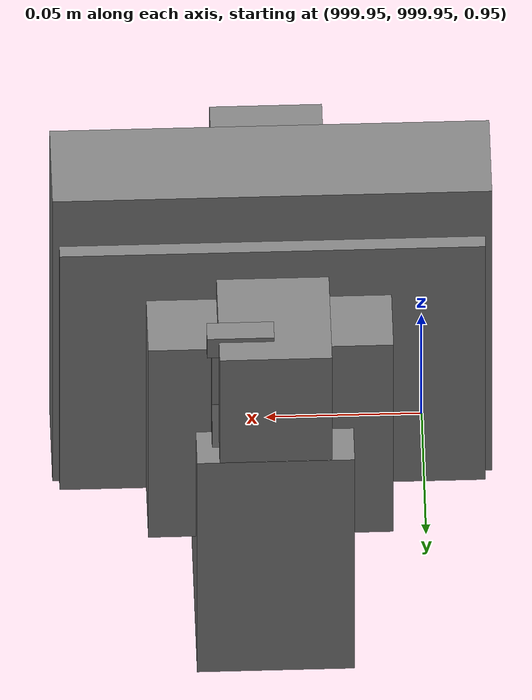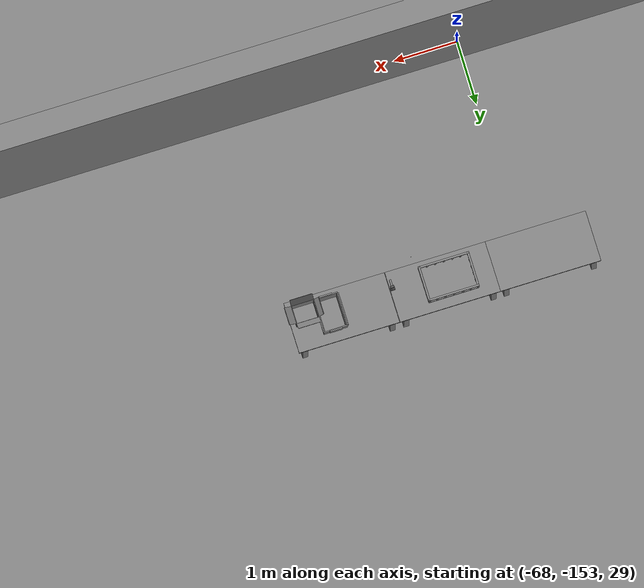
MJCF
<mujoco>
    <option gravity="0.000000000 0.000000000 -9.810000420" timestep="0.0049999999" integrator="implicitfast" density="1.225" viscosity="1.8000001e-05" noslip_iterations="10" iterations="100" sdf_iterations="50">
        <flag multiccd="disable"/>
    </option>
    <size memory="1000M"/>
    <compiler coordinate="local"/>
    <worldbody>
        <light cutoff="30" pos="0 1 1" dir="0 -1 -2"/>
        <light cutoff="30" pos="0 -1 1" dir="0 1 -2"/>
        <body pos="1000.000000000 1000.000000000 1.000000000" euler="0.000000000 0.000000000 180.000000000" name="openloong_gripper_2f85_fix_base_usda_wifi_box">
            <geom contype="1" conaffinity="1" density="1000" type="box" material="" rgba="0.500000000 0.500000000 0.500000000 1.000000000" solimp="0.899999976 0.949999988 0.001000000" friction="1.000000000 0.005000000 0.000100000" solref="0.020000000 1.000000000" margin="0" condim="3" group="0" pos="0.000000000 0.000000000 0.058978677" quat="0.000000000 0.000000047 0.000000000 1.000000000" size="0.068499997 0.018999999 0.059000000" name="openloong_gripper_2f85_fix_base_usda_geom_3E37D47C_E529_4B05_AF86_C8B9075D36B4"/>
            <freejoint name="openloong_gripper_2f85_fix_base_usda_wifi_box_joint"/>
            <site size="0.005000000 0.005000000 0.005000000" rgba="0.500000000 0.500000000 0.500000000 1.000000000" pos="0.000000000 0.000000000 0.000000000" quat="0.999961913 0.008726500 0.000000000 0.000000000" group="0" type="sphere" name="openloong_gripper_2f85_fix_base_usda_wifi_boxsite"/>
        </body>
        <body pos="1000.000000000 1000.000000000 1.000000000" euler="0.000000000 0.000000000 180.000000000" name="openloong_gripper_2f85_fix_base_usda_cpu_fan">
            <geom contype="1" conaffinity="1" density="1000" type="box" material="" rgba="0.500000000 0.500000000 0.500000000 1.000000000" solimp="0.899999976 0.949999988 0.001000000" friction="1.000000000 0.005000000 0.000100000" solref="0.020000000 1.000000000" margin="0" condim="3" group="0" pos="0.000000000 0.000000000 0.070034981" quat="0.000000000 0.000000000 0.000000000 1.000000000" size="0.070700005 0.014699999 0.070700005" name="openloong_gripper_2f85_fix_base_usda_geom_B915AC7D_2A52_4E4B_A85A_C58C96BBB595"/>
            <freejoint name="openloong_gripper_2f85_fix_base_usda_cpu_fan_joint"/>
            <site size="0.005000000 0.005000000 0.005000000" rgba="0.500000000 0.500000000 0.500000000 1.000000000" pos="0.000000000 0.000000000 0.000000000" quat="0.999961913 0.008726535 0.000000000 0.000000000" group="0" type="sphere" name="openloong_gripper_2f85_fix_base_usda_cpu_fancsite"/>
        </body>
        <body pos="-66.329742432 -149.243988037 31.165889740" euler="16.585437775 11.616386414 126.894660950" mocap="true" name="spotlight3_SpotLight"/>
        <body pos="1000.000000000 1000.000000000 1.000000000" euler="0.000011953 0.000005123 -179.999984741" name="openloong_gripper_2f85_fix_base_usda_intel_box">
            <geom contype="1" conaffinity="1" density="1000" type="box" material="" rgba="0.500000000 0.500000000 0.500000000 1.000000000" solimp="0.899999976 0.949999988 0.001000000" friction="1.000000000 0.005000000 0.000100000" solref="0.020000000 1.000000000" margin="0" condim="3" group="0" pos="0.000000000 -0.000067139 0.000082284" quat="0.707106709 0.000000225 0.000000253 0.707106650" size="0.052800003 0.025300000 0.052800003" name="openloong_gripper_2f85_fix_base_usda_geom_231A8A86_81A7_4A65_B9CC_DB3957804EBC"/>
            <freejoint name="openloong_gripper_2f85_fix_base_usda_intel_box_joint"/>
            <site size="0.005000000 0.005000000 0.005000000" rgba="0.500000000 0.500000000 0.500000000 1.000000000" pos="0.000000000 0.000000000 0.000000000" quat="0.999961913 0.008726500 0.000000000 0.000000000" group="0" type="sphere" name="openloong_gripper_2f85_fix_base_usda_intel_boxsite"/>
        </body>
        <body pos="1000.000000000 1000.000000000 1.000000000" euler="0.000000000 0.000000000 180.000000000" name="openloong_gripper_2f85_fix_base_usda_battery_01">
            <geom contype="1" conaffinity="1" density="1000" type="box" material="" rgba="0.500000000 0.500000000 0.500000000 1.000000000" solimp="0.899999976 0.949999988 0.001000000" friction="1.000000000 0.005000000 0.000100000" solref="0.020000000 1.000000000" margin="0" condim="3" group="0" pos="-0.011123657 -0.041940309 0.101691343" quat="1.000000000 0.000000000 0.000000000 0.000000000" size="0.010800000 0.003375000 0.004725000" name="openloong_gripper_2f85_fix_base_usda_geom_D898D513_CD1E_4CB4_9F88_7F2BF311DC27"/>
            <geom contype="1" conaffinity="1" density="1000" type="box" material="" rgba="0.500000000 0.500000000 0.500000000 1.000000000" solimp="0.899999976 0.949999988 0.001000000" friction="1.000000000 0.005000000 0.000100000" solref="0.020000000 1.000000000" margin="0" condim="3" group="0" pos="-0.010876465 -0.044247437 0.047066893" quat="0.998702705 -0.050920475 0.000000000 0.000000000" size="0.009450001 0.002700000 0.024975000" name="openloong_gripper_2f85_fix_base_usda_geom_E538F779_BFA9_454D_A7C6_3DC7A7896801"/>
            <geom contype="1" conaffinity="1" density="1000" type="box" material="" rgba="0.500000000 0.500000000 0.500000000 1.000000000" solimp="0.899999976 0.949999988 0.001000000" friction="1.000000000 0.005000000 0.000100000" solref="0.020000000 1.000000000" margin="0" condim="3" group="0" pos="-0.001235962 -0.000659180 0.047381196" quat="1.000000000 0.000000000 0.000000000 0.000000000" size="0.039420001 0.039150000 0.047250003" name="openloong_gripper_2f85_fix_base_usda_geom_C01403F9_1150_4858_B38F_A83321E67535"/>
            <geom contype="1" conaffinity="1" density="1000" type="box" material="" rgba="0.500000000 0.500000000 0.500000000 1.000000000" solimp="0.899999976 0.949999988 0.001000000" friction="1.000000000 0.005000000 0.000100000" solref="0.020000000 1.000000000" margin="0" condim="3" group="0" pos="-0.010876465 -0.039138794 0.009851727" quat="1.000000000 0.000000000 0.000000000 0.000000000" size="0.009450001 0.010800000 0.013500000" name="openloong_gripper_2f85_fix_base_usda_geom_BC4199C1_3BA2_4FBF_A166_8ED16CDFD505"/>
            <geom contype="1" conaffinity="1" density="1000" type="box" material="" rgba="0.500000000 0.500000000 0.500000000 1.000000000" solimp="0.899999976 0.949999988 0.001000000" friction="1.000000000 0.005000000 0.000100000" solref="0.020000000 1.000000000" margin="0" condim="3" group="0" pos="-0.010876465 -0.041528322 0.071508206" quat="1.000000000 0.000000000 0.000000000 0.000000000" size="0.009450001 0.002700000 0.027000001" name="openloong_gripper_2f85_fix_base_usda_geom_4609FD1A_B059_414B_9BB4_10A172B5CA27"/>
            <freejoint name="openloong_gripper_2f85_fix_base_usda_battery_01_joint"/>
            <site size="0.005000000 0.005000000 0.005000000" rgba="0.500000000 0.500000000 0.500000000 1.000000000" pos="0.000000000 0.000000000 0.000000000" quat="0.999961913 0.008726500 0.000000000 0.000000000" group="0" type="sphere" name="openloong_gripper_2f85_fix_base_usda_battery_01site"/>
        </body>
        <body pos="-66.006385803 -149.150421143 31.166652679" euler="28.986017227 18.232307434 170.841491699" mocap="true" name="spotlight6_SpotLight"/>
        <body pos="1000.000000000 999.999938965 1.000000000" euler="0.000000000 0.000000000 180.000000000" name="openloong_gripper_2f85_fix_base_usda_intelcore_i5">
            <geom contype="1" conaffinity="1" density="1000" type="box" material="" rgba="0.500000000 0.500000000 0.500000000 1.000000000" solimp="0.899999976 0.949999988 0.001000000" friction="1.000000000 0.005000000 0.000100000" solref="0.020000000 1.000000000" margin="0" condim="3" group="0" pos="0.000000000 0.000000000 0.051722717" quat="0.707106709 0.000000000 0.000000000 -0.707106769" size="0.052800000 0.018080002 0.052800000" name="openloong_gripper_2f85_fix_base_usda_geom_6948F855_5B1E_474E_BF93_2BB3EB3853D3"/>
            <freejoint name="openloong_gripper_2f85_fix_base_usda_intelcore_i5_joint"/>
            <site size="0.005000000 0.005000000 0.005000000" rgba="0.500000000 0.500000000 0.500000000 1.000000000" pos="0.000000000 0.000000000 0.000000000" quat="0.999961913 0.008726534 0.000000000 0.000000000" group="0" type="sphere" name="openloong_gripper_2f85_fix_base_usda_intelcore_i5site"/>
        </body>
        <body pos="-66.341995239 -149.567901611 31.162220001" euler="153.380065918 -69.696807861 -108.590591431" mocap="true" name="spotlight2_SpotLight"/>
        <body pos="-64.866622925 -149.383972168 30.183746338" euler="89.999984741 89.999946594 0.000000000" name="openloong_gripper_2f85_fix_base_usda_bluebox_01">
            <geom contype="1" conaffinity="1" density="1000" type="box" material="" rgba="0.500000000 0.500000000 0.500000000 1.000000000" solimp="0.899999976 0.949999988 0.001000000" friction="1.000000000 0.005000000 0.000100000" solref="0.020000000 1.000000000" margin="0" condim="3" group="0" pos="0.276580811 0.187225342 0.000068665" quat="0.707106948 0.000077471 0.707106352 0.000077486" size="0.100000001 0.057999998 0.010000000" name="openloong_gripper_2f85_fix_base_usda_geom_C2EEB5D0_EF9A_4736_B851_B0E7B2767FD5"/>
            <geom contype="1" conaffinity="1" density="1000" type="box" material="" rgba="0.500000000 0.500000000 0.500000000 1.000000000" solimp="0.899999976 0.949999988 0.001000000" friction="1.000000000 0.005000000 0.000100000" solref="0.020000000 1.000000000" margin="0" condim="3" group="0" pos="0.000000000 0.002883911 0.000000000" quat="0.999999881 0.000000000 0.000000000 0.000000000" size="0.254000008 0.003000000 0.172000006" name="openloong_gripper_2f85_fix_base_usda_geom_CD6EF443_6DAA_46E2_A3FD_5100665FA86A"/>
            <geom contype="1" conaffinity="1" density="1000" type="box" material="" rgba="0.500000000 0.500000000 0.500000000 1.000000000" solimp="0.899999976 0.949999988 0.001000000" friction="1.000000000 0.005000000 0.000100000" solref="0.020000000 1.000000000" margin="0" condim="3" group="0" pos="0.000000000 0.124874115 0.173484802" quat="0.999796331 0.020176515 -0.000000015 0.000000030" size="0.259999990 0.119999997 0.007000000" name="openloong_gripper_2f85_fix_base_usda_geom_C116F844_0364_4272_BB2B_62A65BD29187"/>
            <geom contype="1" conaffinity="1" density="1000" type="box" material="" rgba="0.500000000 0.500000000 0.500000000 1.000000000" solimp="0.899999976 0.949999988 0.001000000" friction="1.000000000 0.005000000 0.000100000" solref="0.020000000 1.000000000" margin="0" condim="3" group="0" pos="0.000000000 0.124874115 -0.173469543" quat="0.999796331 -0.020176545 -0.000000015 0.000000000" size="0.259999990 0.119999997 0.007000000" name="openloong_gripper_2f85_fix_base_usda_geom_55AC0D52_A371_48E4_B34D_BB725F08F0F3"/>
            <geom contype="1" conaffinity="1" density="1000" type="box" material="" rgba="0.500000000 0.500000000 0.500000000 1.000000000" solimp="0.899999976 0.949999988 0.001000000" friction="1.000000000 0.005000000 0.000100000" solref="0.020000000 1.000000000" margin="0" condim="3" group="0" pos="0.000000000 0.214008331 0.188980103" quat="0.999912977 0.013176724 0.000000015 0.000000000" size="0.259999990 0.029999999 0.012500000" name="openloong_gripper_2f85_fix_base_usda_geom_29006B0F_CD26_4E9D_9A62_A9F5CB532068"/>
            <geom contype="1" conaffinity="1" density="1000" type="box" material="" rgba="0.500000000 0.500000000 0.500000000 1.000000000" solimp="0.899999976 0.949999988 0.001000000" friction="1.000000000 0.005000000 0.000100000" solref="0.020000000 1.000000000" margin="0" condim="3" group="0" pos="-0.258361816 0.125289917 0.001876831" quat="0.702796936 -0.020792112 0.710783124 0.020769298" size="0.189999998 0.119999997 0.009000000" name="openloong_gripper_2f85_fix_base_usda_geom_97BD8275_214D_4405_95FC_769EA1FE0197"/>
            <geom contype="1" conaffinity="1" density="1000" type="box" material="" rgba="0.500000000 0.500000000 0.500000000 1.000000000" solimp="0.899999976 0.949999988 0.001000000" friction="1.000000000 0.005000000 0.000100000" solref="0.020000000 1.000000000" margin="0" condim="3" group="0" pos="0.000000000 0.214008331 -0.188980103" quat="0.999912977 -0.013176769 0.000000030 0.000000015" size="0.259999990 0.029999999 0.012500000" name="openloong_gripper_2f85_fix_base_usda_geom_B68ACF02_C1B2_4730_A726_F3271B9BFD83"/>
            <geom contype="1" conaffinity="1" density="1000" type="box" material="" rgba="0.500000000 0.500000000 0.500000000 1.000000000" solimp="0.899999976 0.949999988 0.001000000" friction="1.000000000 0.005000000 0.000100000" solref="0.020000000 1.000000000" margin="0" condim="3" group="0" pos="-0.276611328 0.187225342 0.000068665" quat="0.707106650 0.000077441 0.707106709 0.000077456" size="0.100000001 0.057999998 0.010000000" name="openloong_gripper_2f85_fix_base_usda_geom_09B2A077_A73E_4692_BCDE_4D54A9F7002C"/>
            <geom contype="1" conaffinity="1" density="1000" type="box" material="" rgba="0.500000000 0.500000000 0.500000000 1.000000000" solimp="0.899999976 0.949999988 0.001000000" friction="1.000000000 0.005000000 0.000100000" solref="0.020000000 1.000000000" margin="0" condim="3" group="0" pos="0.258331299 0.125289917 0.001876831" quat="0.702851415 0.018856421 0.710823774 -0.019329369" size="0.189999998 0.119999997 0.009000000" name="openloong_gripper_2f85_fix_base_usda_geom_D0830C7B_E51C_4B34_842C_C1F751F1B853"/>
            <freejoint name="openloong_gripper_2f85_fix_base_usda_bluebox_01_joint"/>
            <site size="0.005000000 0.005000000 0.005000000" rgba="0.500000000 0.500000000 0.500000000 1.000000000" pos="0.000000000 0.000000000 0.000000000" quat="0.999961913 0.008726534 0.000000000 0.000000000" group="0" type="sphere" name="openloong_gripper_2f85_fix_base_usda_bluebox_01site"/>
        </body>
        <body pos="-64.496299744 -149.491867065 30.235729218" euler="0.000000000 0.000000000 89.999946594" name="openloong_gripper_2f85_fix_base_usda_cardboardbox_01">
            <geom contype="1" conaffinity="1" density="1000" type="box" material="" rgba="0.500000000 0.500000000 0.500000000 1.000000000" solimp="0.899999976 0.949999988 0.001000000" friction="1.000000000 0.005000000 0.000100000" solref="0.020000000 1.000000000" margin="0" condim="3" group="0" pos="-0.003166199 -0.004086494 0.005052090" quat="1.000000000 0.000000000 0.000000000 0.000000000" size="0.142499998 0.177500010 0.005000000" name="openloong_gripper_2f85_fix_base_usda_geom_0C18732A_1B86_4D06_86BC_315BD00DD412"/>
            <geom contype="1" conaffinity="1" density="1000" type="box" material="" rgba="0.500000000 0.500000000 0.500000000 1.000000000" solimp="0.899999976 0.949999988 0.001000000" friction="1.000000000 0.005000000 0.000100000" solref="0.020000000 1.000000000" margin="0" condim="3" group="0" pos="-0.003166199 0.170316696 0.150570869" quat="1.000000000 0.000000000 0.000000000 0.000000000" size="0.142499998 0.005000000 0.149999991" name="openloong_gripper_2f85_fix_base_usda_geom_804BEFC9_25E8_486A_84F0_6129739EEAFA"/>
            <geom contype="1" conaffinity="1" density="1000" type="box" material="" rgba="0.500000000 0.500000000 0.500000000 1.000000000" solimp="0.899999976 0.949999988 0.001000000" friction="1.000000000 0.005000000 0.000100000" solref="0.020000000 1.000000000" margin="0" condim="3" group="0" pos="-0.147399902 -0.005307198 0.150570869" quat="1.000000000 0.000000000 0.000000000 0.000000000" size="0.005000000 0.177500010 0.149999991" name="openloong_gripper_2f85_fix_base_usda_geom_73E52510_0B14_447E_A4EA_6AF251FA049D"/>
            <geom contype="1" conaffinity="1" density="1000" type="box" material="" rgba="0.500000000 0.500000000 0.500000000 1.000000000" solimp="0.899999976 0.949999988 0.001000000" friction="1.000000000 0.005000000 0.000100000" solref="0.020000000 1.000000000" margin="0" condim="3" group="0" pos="0.140275955 -0.005307198 0.150570869" quat="1.000000000 0.000000000 0.000000000 0.000000000" size="0.005000000 0.177500010 0.149999991" name="openloong_gripper_2f85_fix_base_usda_geom_EB9DA109_E66E_452D_B037_AA3A7FF3676E"/>
            <geom contype="1" conaffinity="1" density="1000" type="box" material="" rgba="0.500000000 0.500000000 0.500000000 1.000000000" solimp="0.899999976 0.949999988 0.001000000" friction="1.000000000 0.005000000 0.000100000" solref="0.020000000 1.000000000" margin="0" condim="3" group="0" pos="-0.003166199 -0.181550980 0.150570869" quat="1.000000000 0.000000000 0.000000000 0.000000000" size="0.142499998 0.005000000 0.149999991" name="openloong_gripper_2f85_fix_base_usda_geom_7246139C_0BC2_4246_93F7_8A7F65408DFF"/>
            <freejoint name="openloong_gripper_2f85_fix_base_usda_cardboardbox_01_joint"/>
            <site size="0.005000000 0.005000000 0.005000000" rgba="0.500000000 0.500000000 0.500000000 1.000000000" pos="0.000000000 0.000000000 0.000000000" quat="0.999961913 0.008726535 0.000000000 0.000000000" group="0" type="sphere" name="openloong_gripper_2f85_fix_base_usda_site_48B8EBC1_0345_4A36_9010_9AB8EBB1E545"/>
            <body pos="0.139160156 -0.004048347 0.301930904" euler="-179.999954224 49.383502960 179.999954224" name="openloong_gripper_2f85_fix_base_usda_A1_006">
                <geom contype="1" conaffinity="1" density="1000" type="box" material="" rgba="0.500000000 0.500000000 0.500000000 1.000000000" solimp="0.899999976 0.949999988 0.001000000" friction="1.000000000 0.005000000 0.000100000" solref="0.020000000 1.000000000" margin="0" condim="3" group="0" pos="-0.071587563 0.000009537 0.001745224" quat="0.999999881 0.000000000 0.000000000 0.000000000" size="0.071249999 0.179999992 0.002500000" name="openloong_gripper_2f85_fix_base_usda_geom_F8651587_0DD7_41C2_BEBF_C4F62975FF62"/>
                <joint armature="0" stiffness="0.07" damping="0.0099999998" axis="0.000000 1.000000 0.000000" type="hinge" name="openloong_gripper_2f85_fix_base_usda_A1_006"/>
            </body>
            <body pos="-0.145902634 -0.004086494 0.301938057" euler="-180.000000000 -60.000011444 -180.000000000" name="openloong_gripper_2f85_fix_base_usda_A2_006">
                <geom contype="1" conaffinity="1" density="1000" type="box" material="" rgba="0.500000000 0.500000000 0.500000000 1.000000000" solimp="0.899999976 0.949999988 0.001000000" friction="1.000000000 0.005000000 0.000100000" solref="0.020000000 1.000000000" margin="0" condim="3" group="0" pos="0.071268082 0.000009537 0.002717972" quat="0.000002921 0.000000000 -0.000000030 0.999999881" size="0.071249999 0.179999992 0.002500000" name="openloong_gripper_2f85_fix_base_usda_geom_F68411EA_ED7D_4A5A_A31C_11434E47331F"/>
                <joint armature="0" stiffness="0.07" damping="0.0099999998" axis="0.000000 1.000000 0.000000" type="hinge" name="openloong_gripper_2f85_fix_base_usda_A2_006"/>
            </body>
            <body pos="-0.003385544 0.175991058 0.301930904" euler="-125.858116150 -0.000004561 0.000002331" name="openloong_gripper_2f85_fix_base_usda_B2_006">
                <geom contype="1" conaffinity="1" density="1000" type="box" material="" rgba="0.500000000 0.500000000 0.500000000 1.000000000" solimp="0.899999976 0.949999988 0.001000000" friction="1.000000000 0.005000000 0.000100000" solref="0.020000000 1.000000000" margin="0" condim="3" group="0" pos="0.000009537 -0.070939064 -0.002470016" quat="0.999614120 0.027776197 -0.000000015 0.000000030" size="0.137500003 0.064999998 0.005000000" name="openloong_gripper_2f85_fix_base_usda_geom_03C8C9A2_0364_4AE9_92A5_E50C05DD3E01"/>
                <joint armature="0" stiffness="0.07" damping="0.0099999998" axis="1.000000 0.000000 0.000000" type="hinge" name="openloong_gripper_2f85_fix_base_usda_B2_006"/>
            </body>
            <body pos="-0.003385544 -0.184140205 0.301938057" euler="147.805557251 0.000000000 0.000000000" name="openloong_gripper_2f85_fix_base_usda_B1_006">
                <geom contype="1" conaffinity="1" density="1000" type="box" material="" rgba="0.500000000 0.500000000 0.500000000 1.000000000" solimp="0.899999976 0.949999988 0.001000000" friction="1.000000000 0.005000000 0.000100000" solref="0.020000000 1.000000000" margin="0" condim="3" group="0" pos="-0.000028610 0.070202351 -0.002703667" quat="0.999614179 -0.027776167 0.000000000 0.000000000" size="0.137500003 0.064999998 0.005000000" name="openloong_gripper_2f85_fix_base_usda_geom_1463A8B9_48CC_4470_B5C3_5B198C1360CA"/>
                <joint armature="0" stiffness="0.07" damping="0.0099999998" axis="1.000000 0.000000 0.000000" type="hinge" name="openloong_gripper_2f85_fix_base_usda_B1_006"/>
            </body>
        </body>
        <body pos="-65.882858276 -149.481979370 30.229999542" euler="-64.487716675 0.000000000 0.000000000" name="openloong_gripper_2f85_fix_base_usda_Barcode">
            <geom contype="1" conaffinity="1" density="1000" type="box" material="" rgba="0.500000000 0.500000000 0.500000000 1.000000000" solimp="0.899999976 0.949999988 0.001000000" friction="1.000000000 0.005000000 0.000100000" solref="0.020000000 1.000000000" margin="0" condim="3" group="0" pos="0.000000000 0.013038635 0.001419067" quat="0.000000000 0.000000000 0.000000000 1.000000119" size="0.034000002 0.010000000 0.017999999" name="openloong_gripper_2f85_fix_base_usda_geom_45687EE9_4C41_409E_A00C_8FA6111A6DEB"/>
            <geom contype="1" conaffinity="1" density="1000" type="box" material="" rgba="0.500000000 0.500000000 0.500000000 1.000000000" solimp="0.899999976 0.949999988 0.001000000" friction="1.000000000 0.005000000 0.000100000" solref="0.020000000 1.000000000" margin="0" condim="3" group="0" pos="0.000000000 -0.035301208 -0.007095337" quat="0.000000000 0.000000000 -0.043619365 0.999048233" size="0.028999999 0.010000000 0.020000000" name="openloong_gripper_2f85_fix_base_usda_geom_C72F33F6_3811_4993_8815_1EF731637BDD"/>
            <geom contype="1" conaffinity="1" density="1000" type="box" material="" rgba="0.500000000 0.500000000 0.500000000 1.000000000" solimp="0.899999976 0.949999988 0.001000000" friction="1.000000000 0.005000000 0.000100000" solref="0.020000000 1.000000000" margin="0" condim="3" group="0" pos="0.000000000 -0.043411255 -0.011749268" quat="0.922262907 0.386563420 0.000000000 0.000000000" size="0.026000001 0.010000000 0.020000000" name="openloong_gripper_2f85_fix_base_usda_geom_B67C4217_EBCB_4270_8149_B977E80BD196"/>
            <geom contype="1" conaffinity="1" density="1000" type="box" material="" rgba="0.500000000 0.500000000 0.500000000 1.000000000" solimp="0.899999976 0.949999988 0.001000000" friction="1.000000000 0.005000000 0.000100000" solref="0.020000000 1.000000000" margin="0" condim="3" group="0" pos="0.000000000 -0.016967773 -0.031860352" quat="0.000000000 0.000000000 0.000000000 1.000000119" size="0.008000000 0.010000000 0.013000000" name="openloong_gripper_2f85_fix_base_usda_geom_BA94B196_904E_4678_B366_54115C8154D4"/>
            <geom contype="1" conaffinity="1" density="1000" type="box" material="" rgba="0.500000000 0.500000000 0.500000000 1.000000000" solimp="0.899999976 0.949999988 0.001000000" friction="1.000000000 0.005000000 0.000100000" solref="0.020000000 1.000000000" margin="0" condim="3" group="0" pos="0.000000000 -0.001869202 0.000312805" quat="0.953716993 0.300705761 0.000000000 0.000000000" size="0.032000002 0.010000000 0.018999999" name="openloong_gripper_2f85_fix_base_usda_geom_D2AA10EB_9B03_4049_B2D6_F0A319F0E8D8"/>
            <geom contype="1" conaffinity="1" density="1000" type="box" material="" rgba="0.500000000 0.500000000 0.500000000 1.000000000" solimp="0.899999976 0.949999988 0.001000000" friction="1.000000000 0.005000000 0.000100000" solref="0.020000000 1.000000000" margin="0" condim="3" group="0" pos="0.000000000 -0.019531250 -0.003173828" quat="0.953716993 0.300705761 0.000000000 0.000000000" size="0.030999999 0.010000000 0.020000000" name="openloong_gripper_2f85_fix_base_usda_geom_7F176061_830A_4A28_8B24_D11E72778D0E"/>
            <geom contype="1" conaffinity="1" density="1000" type="box" material="" rgba="0.500000000 0.500000000 0.500000000 1.000000000" solimp="0.899999976 0.949999988 0.001000000" friction="1.000000000 0.005000000 0.000100000" solref="0.020000000 1.000000000" margin="0" condim="3" group="0" pos="0.000000000 -0.035301208 -0.007095337" quat="0.953716993 0.300705761 0.000000000 0.000000000" size="0.028999999 0.010000000 0.020000000" name="openloong_gripper_2f85_fix_base_usda_geom_EADCD30B_E631_4C14_B5B9_BCAFE0B07CB1"/>
            <geom contype="1" conaffinity="1" density="1000" type="box" material="" rgba="0.500000000 0.500000000 0.500000000 1.000000000" solimp="0.899999976 0.949999988 0.001000000" friction="1.000000000 0.005000000 0.000100000" solref="0.020000000 1.000000000" margin="0" condim="3" group="0" pos="0.000000000 -0.042617798 -0.071121216" quat="0.000000000 0.000000000 0.000000000 1.000000119" size="0.013000000 0.021000000 0.059999999" name="openloong_gripper_2f85_fix_base_usda_geom_C586F457_F9F3_4F32_AC8F_30D5DB280193"/>
            <freejoint name="openloong_gripper_2f85_fix_base_usda_Barcode_joint"/>
            <site size="0.005000000 0.005000000 0.005000000" rgba="0.500000000 0.500000000 0.500000000 1.000000000" pos="0.000000000 0.000000000 0.000000000" quat="1.000000000 0.000000000 0.000000000 0.000000000" group="0" type="sphere" name="openloong_gripper_2f85_fix_base_usda_Barcode_site"/>
        </body>
        <body pos="-66.745018005 -149.392349243 30.184000015" euler="0.000000000 0.000000000 89.999946594" name="[22331310731223]_Basket_01">
            <geom contype="1" conaffinity="1" density="1000" type="box" material="" rgba="0.500000000 0.500000000 0.500000000 1.000000000" solimp="0.899999976 0.949999988 0.001000000" friction="1.000000000 0.005000000 0.000100000" solref="0.020000000 1.000000000" margin="0" condim="3" group="0" pos="-0.052425385 0.389207840 0.089787483" quat="0.707107008 0.000000000 0.000000000 0.707106411" size="0.014249999 0.014249999 0.059999999" name="[22331310731223]_geom_CFB2AB63_43CF_4A12_B856_488FE2F7F6AA"/>
            <geom contype="1" conaffinity="1" density="1000" type="box" material="" rgba="0.500000000 0.500000000 0.500000000 1.000000000" solimp="0.899999976 0.949999988 0.001000000" friction="1.000000000 0.005000000 0.000100000" solref="0.020000000 1.000000000" margin="0" condim="3" group="0" pos="0.264015198 -0.133043289 0.089787483" quat="0.707107008 0.000000000 0.000000000 0.707106411" size="0.014249999 0.014249999 0.059999999" name="[22331310731223]_geom_B9BBBE31_BC68_4E6B_A70A_A034E3B8118B"/>
            <geom contype="1" conaffinity="1" density="1000" type="box" material="" rgba="0.500000000 0.500000000 0.500000000 1.000000000" solimp="0.899999976 0.949999988 0.001000000" friction="1.000000000 0.005000000 0.000100000" solref="0.020000000 1.000000000" margin="0" condim="3" group="0" pos="-0.264015198 -0.265548706 0.089793205" quat="0.707107008 0.000000000 0.000000000 0.707106411" size="0.014249999 0.014249999 0.059999999" name="[22331310731223]_geom_6DCF31F3_4BFC_454B_871F_E940BC03127C"/>
            <geom contype="1" conaffinity="1" density="1000" type="box" material="" rgba="0.500000000 0.500000000 0.500000000 1.000000000" solimp="0.899999976 0.949999988 0.001000000" friction="1.000000000 0.005000000 0.000100000" solref="0.020000000 1.000000000" margin="0" condim="3" group="0" pos="-0.160263062 -0.389322281 0.089793205" quat="0.707107008 0.000000000 0.000000000 0.707106411" size="0.014249999 0.014249999 0.059999999" name="[22331310731223]_geom_F9C7E758_FA58_44F5_BBCA_0300AED84436"/>
            <geom contype="1" conaffinity="1" density="1000" type="box" material="" rgba="0.500000000 0.500000000 0.500000000 1.000000000" solimp="0.899999976 0.949999988 0.001000000" friction="1.000000000 0.005000000 0.000100000" solref="0.020000000 1.000000000" margin="0" condim="3" group="0" pos="0.162265778 -0.389322281 0.089787483" quat="0.707107008 0.000000000 0.000000000 0.707106411" size="0.014249999 0.014249999 0.059999999" name="[22331310731223]_geom_917D53AE_40FD_41DC_9788_E2B3832630B6"/>
            <geom contype="1" conaffinity="1" density="1000" type="box" material="" rgba="0.500000000 0.500000000 0.500000000 1.000000000" solimp="0.899999976 0.949999988 0.001000000" friction="1.000000000 0.005000000 0.000100000" solref="0.020000000 1.000000000" margin="0" condim="3" group="0" pos="0.264015198 0.389207840 0.089787483" quat="0.707107008 0.000000000 0.000000000 0.707106411" size="0.014249999 0.014249999 0.059999999" name="[22331310731223]_geom_7E528E1C_8547_4073_A241_81CB52CAE0A3"/>
            <geom contype="1" conaffinity="1" density="1000" type="box" material="" rgba="0.500000000 0.500000000 0.500000000 1.000000000" solimp="0.899999976 0.949999988 0.001000000" friction="1.000000000 0.005000000 0.000100000" solref="0.020000000 1.000000000" margin="0" condim="3" group="0" pos="-0.264015198 -0.133043289 0.089793205" quat="0.707107008 0.000000000 0.000000000 0.707106411" size="0.014249999 0.014249999 0.059999999" name="[22331310731223]_geom_C518ECEA_8040_4018_BCE9_ADDE619F9D96"/>
            <geom contype="1" conaffinity="1" density="1000" type="box" material="" rgba="0.500000000 0.500000000 0.500000000 1.000000000" solimp="0.899999976 0.949999988 0.001000000" friction="1.000000000 0.005000000 0.000100000" solref="0.020000000 1.000000000" margin="0" condim="3" group="0" pos="-0.264026642 0.269256592 0.089793205" quat="0.707107008 0.000000000 0.000000000 0.707106411" size="0.014249999 0.014249999 0.059999999" name="[22331310731223]_geom_27B79770_F81B_4F8C_9F3C_BC9AE131AA4E"/>
            <geom contype="1" conaffinity="1" density="1000" type="box" material="" rgba="0.500000000 0.500000000 0.500000000 1.000000000" solimp="0.899999976 0.949999988 0.001000000" friction="1.000000000 0.005000000 0.000100000" solref="0.020000000 1.000000000" margin="0" condim="3" group="0" pos="0.054462433 0.389207840 0.089787483" quat="0.707107008 0.000000000 0.000000000 0.707106411" size="0.014249999 0.014249999 0.059999999" name="[22331310731223]_geom_D5E7B294_0DDD_4FD7_AF96_D7CCC5A9B067"/>
            <geom contype="1" conaffinity="1" density="1000" type="box" material="" rgba="0.500000000 0.500000000 0.500000000 1.000000000" solimp="0.899999976 0.949999988 0.001000000" friction="1.000000000 0.005000000 0.000100000" solref="0.020000000 1.000000000" margin="0" condim="3" group="0" pos="0.054462433 -0.389322281 0.089787483" quat="0.707107008 0.000000000 0.000000000 0.707106411" size="0.014249999 0.014249999 0.059999999" name="[22331310731223]_geom_715D898F_4CE4_4ABD_A797_734EDBA3624A"/>
            <geom contype="1" conaffinity="1" density="1000" type="box" material="" rgba="0.500000000 0.500000000 0.500000000 1.000000000" solimp="0.899999976 0.949999988 0.001000000" friction="1.000000000 0.005000000 0.000100000" solref="0.020000000 1.000000000" margin="0" condim="3" group="0" pos="0.264015198 0.269256592 0.089793205" quat="0.707107008 0.000000000 0.000000000 0.707106411" size="0.014249999 0.014249999 0.059999999" name="[22331310731223]_geom_B0203A6F_E810_49A7_8B5C_4850B1E7D9C1"/>
            <geom contype="1" conaffinity="1" density="1000" type="box" material="" rgba="0.500000000 0.500000000 0.500000000 1.000000000" solimp="0.899999976 0.949999988 0.001000000" friction="1.000000000 0.005000000 0.000100000" solref="0.020000000 1.000000000" margin="0" condim="3" group="0" pos="0.264015198 -0.389322281 0.089787483" quat="0.707107008 0.000000000 0.000000000 0.707106411" size="0.014249999 0.014249999 0.059999999" name="[22331310731223]_geom_9D5F1280_0B90_468A_892F_BA781257E4B7"/>
            <geom contype="1" conaffinity="1" density="1000" type="box" material="" rgba="0.500000000 0.500000000 0.500000000 1.000000000" solimp="0.899999976 0.949999988 0.001000000" friction="1.000000000 0.005000000 0.000100000" solref="0.020000000 1.000000000" margin="0" condim="3" group="0" pos="0.000000000 0.000000000 0.015998840" quat="0.707107008 0.000000000 0.000000000 0.707106411" size="0.403499991 0.279000014 0.015750000" name="[22331310731223]_geom_F139C5F5_EB9D_4A46_9316_71F84D535A1E"/>
            <geom contype="1" conaffinity="1" density="1000" type="box" material="" rgba="0.500000000 0.500000000 0.500000000 1.000000000" solimp="0.899999976 0.949999988 0.001000000" friction="1.000000000 0.005000000 0.000100000" solref="0.020000000 1.000000000" margin="0" condim="3" group="0" pos="0.000000000 -0.389476776 0.163619041" quat="0.707107008 0.000000000 0.000000000 0.707106411" size="0.015000000 0.277500004 0.015750000" name="[22331310731223]_geom_6834558C_BD43_46EE_B16C_2BDE427D99F1"/>
            <geom contype="1" conaffinity="1" density="1000" type="box" material="" rgba="0.500000000 0.500000000 0.500000000 1.000000000" solimp="0.899999976 0.949999988 0.001000000" friction="1.000000000 0.005000000 0.000100000" solref="0.020000000 1.000000000" margin="0" condim="3" group="0" pos="0.162265778 0.389207840 0.089787483" quat="0.707107008 0.000000000 0.000000000 0.707106411" size="0.014249999 0.014249999 0.059999999" name="[22331310731223]_geom_C74909BD_562B_4E3E_9476_2F509E133C85"/>
            <geom contype="1" conaffinity="1" density="1000" type="box" material="" rgba="0.500000000 0.500000000 0.500000000 1.000000000" solimp="0.899999976 0.949999988 0.001000000" friction="1.000000000 0.005000000 0.000100000" solref="0.020000000 1.000000000" margin="0" condim="3" group="0" pos="0.000000000 0.389471054 0.163619041" quat="0.707107008 0.000000000 0.000000000 0.707106411" size="0.015000000 0.277500004 0.015750000" name="[22331310731223]_geom_26DA862B_3A16_4CB5_956F_0BC143D0CB3A"/>
            <geom contype="1" conaffinity="1" density="1000" type="box" material="" rgba="0.500000000 0.500000000 0.500000000 1.000000000" solimp="0.899999976 0.949999988 0.001000000" friction="1.000000000 0.005000000 0.000100000" solref="0.020000000 1.000000000" margin="0" condim="3" group="0" pos="-0.263511658 0.000000000 0.163619041" quat="0.707107008 0.000000000 0.000000000 0.707106411" size="0.403499991 0.015000000 0.015750000" name="[22331310731223]_geom_8F3EF561_54A2_4C08_8B3B_4763DEBC505E"/>
            <geom contype="1" conaffinity="1" density="1000" type="box" material="" rgba="0.500000000 0.500000000 0.500000000 1.000000000" solimp="0.899999976 0.949999988 0.001000000" friction="1.000000000 0.005000000 0.000100000" solref="0.020000000 1.000000000" margin="0" condim="3" group="0" pos="-0.264015198 0.141334534 0.089793205" quat="0.707107008 0.000000000 0.000000000 0.707106411" size="0.014249999 0.014249999 0.059999999" name="[22331310731223]_geom_F343099E_D4D6_4ADB_A700_D825E276F15D"/>
            <geom contype="1" conaffinity="1" density="1000" type="box" material="" rgba="0.500000000 0.500000000 0.500000000 1.000000000" solimp="0.899999976 0.949999988 0.001000000" friction="1.000000000 0.005000000 0.000100000" solref="0.020000000 1.000000000" margin="0" condim="3" group="0" pos="0.264015198 -0.265548706 0.089787483" quat="0.707107008 0.000000000 0.000000000 0.707106411" size="0.014249999 0.014249999 0.059999999" name="[22331310731223]_geom_5D6F89B5_69AA_4649_9BFC_845C34E4CC5D"/>
            <geom contype="1" conaffinity="1" density="1000" type="box" material="" rgba="0.500000000 0.500000000 0.500000000 1.000000000" solimp="0.899999976 0.949999988 0.001000000" friction="1.000000000 0.005000000 0.000100000" solref="0.020000000 1.000000000" margin="0" condim="3" group="0" pos="-0.160263062 0.389207840 0.089787483" quat="0.707107008 0.000000000 0.000000000 0.707106411" size="0.014249999 0.014249999 0.059999999" name="[22331310731223]_geom_034FB054_58DB_403B_9840_58ECC85120E0"/>
            <geom contype="1" conaffinity="1" density="1000" type="box" material="" rgba="0.500000000 0.500000000 0.500000000 1.000000000" solimp="0.899999976 0.949999988 0.001000000" friction="1.000000000 0.005000000 0.000100000" solref="0.020000000 1.000000000" margin="0" condim="3" group="0" pos="-0.052425385 -0.389322281 0.089787483" quat="0.707107008 0.000000000 0.000000000 0.707106411" size="0.014249999 0.014249999 0.059999999" name="[22331310731223]_geom_4F0F0EB9_EAE0_4D95_B939_9006B4343DE5"/>
            <geom contype="1" conaffinity="1" density="1000" type="box" material="" rgba="0.500000000 0.500000000 0.500000000 1.000000000" solimp="0.899999976 0.949999988 0.001000000" friction="1.000000000 0.005000000 0.000100000" solref="0.020000000 1.000000000" margin="0" condim="3" group="0" pos="-0.264026642 -0.389322281 0.089793205" quat="0.707107008 0.000000000 0.000000000 0.707106411" size="0.014249999 0.014249999 0.059999999" name="[22331310731223]_geom_228CBC6D_FDE5_4D23_A035_47A617DC0142"/>
            <geom contype="1" conaffinity="1" density="1000" type="box" material="" rgba="0.500000000 0.500000000 0.500000000 1.000000000" solimp="0.899999976 0.949999988 0.001000000" friction="1.000000000 0.005000000 0.000100000" solref="0.020000000 1.000000000" margin="0" condim="3" group="0" pos="0.264015198 0.141334534 0.089787483" quat="0.707107008 0.000000000 0.000000000 0.707106411" size="0.014249999 0.014249999 0.059999999" name="[22331310731223]_geom_A648E053_F054_4E13_B9C1_F959432E67C5"/>
            <geom contype="1" conaffinity="1" density="1000" type="box" material="" rgba="0.500000000 0.500000000 0.500000000 1.000000000" solimp="0.899999976 0.949999988 0.001000000" friction="1.000000000 0.005000000 0.000100000" solref="0.020000000 1.000000000" margin="0" condim="3" group="0" pos="-0.264015198 0.389207840 0.089793205" quat="0.707107008 0.000000000 0.000000000 0.707106411" size="0.014249999 0.014249999 0.059999999" name="[22331310731223]_geom_4B0DB36E_FE20_4A4B_927D_C4497A853688"/>
            <geom contype="1" conaffinity="1" density="1000" type="box" material="" rgba="0.500000000 0.500000000 0.500000000 1.000000000" solimp="0.899999976 0.949999988 0.001000000" friction="1.000000000 0.005000000 0.000100000" solref="0.020000000 1.000000000" margin="0" condim="3" group="0" pos="0.264015198 0.004480362 0.089787483" quat="0.707107008 0.000000000 0.000000000 0.707106411" size="0.014249999 0.014249999 0.059999999" name="[22331310731223]_geom_2FBD6800_0CF1_40F2_9F64_3F9585CF2F58"/>
            <geom contype="1" conaffinity="1" density="1000" type="box" material="" rgba="0.500000000 0.500000000 0.500000000 1.000000000" solimp="0.899999976 0.949999988 0.001000000" friction="1.000000000 0.005000000 0.000100000" solref="0.020000000 1.000000000" margin="0" condim="3" group="0" pos="0.263694763 -0.000011444 0.163619041" quat="0.707107008 0.000000000 0.000000000 0.707106411" size="0.403499991 0.015000000 0.015750000" name="[22331310731223]_geom_976FFF13_6957_4660_BF97_1C5C9117E2D8"/>
            <geom contype="1" conaffinity="1" density="1000" type="box" material="" rgba="0.500000000 0.500000000 0.500000000 1.000000000" solimp="0.899999976 0.949999988 0.001000000" friction="1.000000000 0.005000000 0.000100000" solref="0.020000000 1.000000000" margin="0" condim="3" group="0" pos="-0.264015198 0.004480362 0.089793205" quat="0.707107008 0.000000000 0.000000000 0.707106411" size="0.014249999 0.014249999 0.059999999" name="[22331310731223]_geom_16938CB8_7B87_421D_9438_390BB297AE98"/>
            <freejoint name="[22331310731223]_joint_8F9C22B8_24EB_4198_81B9_3F45CBAC3578"/>
        </body>
        <body pos="0.000000000 0.000000000 0.000000000" euler="0.000000000 0.000000000 0.000000000" name="Static Objects_Static Objects">
            <geom contype="1" conaffinity="1" density="1000" type="box" material="" rgba="0.500000000 0.500000000 0.500000000 1.000000000" solimp="0.899999976 0.949999988 0.001000000" friction="1.000000000 0.005000000 0.000100000" solref="0.020000000 1.000000000" margin="0" condim="3" group="0" pos="-67.544113159 -149.365814209 29.727830887" quat="0.500000417 0.499999970 0.499999553 0.499999970" size="0.381000012 0.319999993 0.041000001" name="Static Objects_geom_C29779A8_D405_4539_BDFB_75C7698A1410"/>
            <geom contype="1" conaffinity="1" density="1000" type="box" material="" rgba="0.500000000 0.500000000 0.500000000 1.000000000" solimp="0.899999976 0.949999988 0.001000000" friction="1.000000000 0.005000000 0.000100000" solref="0.020000000 1.000000000" margin="0" condim="3" group="0" pos="-68.239501953 -149.365814209 30.086868286" quat="0.500000417 0.499999970 0.499999553 0.499999970" size="0.370999992 0.039500002 0.745000005" name="Static Objects_geom_5A0029EF_A816_491A_A5E3_85993FA11111"/>
            <geom contype="1" conaffinity="1" density="1000" type="box" material="" rgba="0.500000000 0.500000000 0.500000000 1.000000000" solimp="0.899999976 0.949999988 0.001000000" friction="1.000000000 0.005000000 0.000100000" solref="0.020000000 1.000000000" margin="0" condim="3" group="0" pos="-68.239501953 -149.365814209 30.147235870" quat="0.500000417 0.499999970 0.499999553 0.499999970" size="0.400000006 0.022000000 0.800000012" name="Static Objects_geom_26CA1D7A_B762_41E6_9998_FB2346D35D76"/>
            <geom contype="1" conaffinity="1" density="1000" type="box" material="" rgba="0.500000000 0.500000000 0.500000000 1.000000000" solimp="0.899999976 0.949999988 0.001000000" friction="1.000000000 0.005000000 0.000100000" solref="0.020000000 1.000000000" margin="0" condim="3" group="0" pos="-68.934890747 -149.365814209 29.727830887" quat="0.500000417 0.499999970 0.499999553 0.499999970" size="0.381000012 0.319999993 0.041000001" name="Static Objects_geom_730E03E6_59EF_4869_92FC_F9796C4050D0"/>
            <geom contype="1" conaffinity="1" density="1000" type="box" material="" rgba="0.500000000 0.500000000 0.500000000 1.000000000" solimp="0.899999976 0.949999988 0.001000000" friction="1.000000000 0.005000000 0.000100000" solref="0.020000000 1.000000000" margin="0" condim="3" group="0" pos="-68.239501953 -149.365814209 29.561563492" quat="0.500000417 0.499999970 0.499999553 0.499999970" size="0.020000000 0.022000000 0.660000026" name="Static Objects_geom_9FDEFD16_4748_42FF_95C3_0519585A3FAD"/>
            <geom contype="1" conaffinity="1" density="1000" type="box" material="" rgba="0.500000000 0.500000000 0.500000000 1.000000000" solimp="0.899999976 0.949999988 0.001000000" friction="1.000000000 0.005000000 0.000100000" solref="0.020000000 1.000000000" margin="0" condim="3" group="0" pos="-65.945671082 -149.365814209 29.727830887" quat="0.500000417 0.499999970 0.499999553 0.499999970" size="0.381000012 0.319999993 0.041000001" name="Static Objects_geom_384AD298_6ED8_42C5_8330_1BA2E46C84BE"/>
            <geom contype="1" conaffinity="1" density="1000" type="box" material="" rgba="0.500000000 0.500000000 0.500000000 1.000000000" solimp="0.899999976 0.949999988 0.001000000" friction="1.000000000 0.005000000 0.000100000" solref="0.020000000 1.000000000" margin="0" condim="3" group="0" pos="-66.641059875 -149.365814209 30.086868286" quat="0.500000417 0.499999970 0.499999553 0.499999970" size="0.370999992 0.039500002 0.745000005" name="Static Objects_geom_904CB47F_B724_4092_B663_BB3FEEC69754"/>
            <geom contype="1" conaffinity="1" density="1000" type="box" material="" rgba="0.500000000 0.500000000 0.500000000 1.000000000" solimp="0.899999976 0.949999988 0.001000000" friction="1.000000000 0.005000000 0.000100000" solref="0.020000000 1.000000000" margin="0" condim="3" group="0" pos="-66.641059875 -149.365814209 30.147235870" quat="0.500000417 0.499999970 0.499999553 0.499999970" size="0.400000006 0.022000000 0.800000012" name="Static Objects_geom_267CB05F_28A7_4AEB_AE0E_F1FA8834BA9C"/>
            <geom contype="1" conaffinity="1" density="1000" type="box" material="" rgba="0.500000000 0.500000000 0.500000000 1.000000000" solimp="0.899999976 0.949999988 0.001000000" friction="1.000000000 0.005000000 0.000100000" solref="0.020000000 1.000000000" margin="0" condim="3" group="0" pos="-67.336448669 -149.365814209 29.727830887" quat="0.500000417 0.499999970 0.499999553 0.499999970" size="0.381000012 0.319999993 0.041000001" name="Static Objects_geom_ECFC8429_73DC_415E_BAA7_A38785E8D8DB"/>
            <geom contype="1" conaffinity="1" density="1000" type="box" material="" rgba="0.500000000 0.500000000 0.500000000 1.000000000" solimp="0.899999976 0.949999988 0.001000000" friction="1.000000000 0.005000000 0.000100000" solref="0.020000000 1.000000000" margin="0" condim="3" group="0" pos="-66.641059875 -149.365814209 29.561563492" quat="0.500000417 0.499999970 0.499999553 0.499999970" size="0.020000000 0.022000000 0.660000026" name="Static Objects_geom_4F8330AA_F3EE_43CB_A29C_BBCFB17A74F2"/>
            <geom contype="1" conaffinity="1" density="1000" type="box" material="" rgba="0.500000000 0.500000000 0.500000000 1.000000000" solimp="0.899999976 0.949999988 0.001000000" friction="1.000000000 0.005000000 0.000100000" solref="0.020000000 1.000000000" margin="0" condim="3" group="0" pos="-64.338577271 -149.365814209 29.727830887" quat="0.500000417 0.499999970 0.499999553 0.499999970" size="0.381000012 0.319999993 0.041000001" name="Static Objects_geom_60952CDF_A0E7_4B29_9429_3F0198BC1E65"/>
            <geom contype="1" conaffinity="1" density="1000" type="box" material="" rgba="0.500000000 0.500000000 0.500000000 1.000000000" solimp="0.899999976 0.949999988 0.001000000" friction="1.000000000 0.005000000 0.000100000" solref="0.020000000 1.000000000" margin="0" condim="3" group="0" pos="-65.033966064 -149.365814209 30.086868286" quat="0.500000417 0.499999970 0.499999553 0.499999970" size="0.370999992 0.039500002 0.745000005" name="Static Objects_geom_5C2C86E0_6840_4D6F_B52E_AD1A4A469FFD"/>
            <geom contype="1" conaffinity="1" density="1000" type="box" material="" rgba="0.500000000 0.500000000 0.500000000 1.000000000" solimp="0.899999976 0.949999988 0.001000000" friction="1.000000000 0.005000000 0.000100000" solref="0.020000000 1.000000000" margin="0" condim="3" group="0" pos="-65.033966064 -149.365814209 30.147235870" quat="0.500000417 0.499999970 0.499999553 0.499999970" size="0.400000006 0.022000000 0.800000012" name="Static Objects_geom_CD4C6ED9_8216_4700_B806_583BB431EDD2"/>
            <geom contype="1" conaffinity="1" density="1000" type="box" material="" rgba="0.500000000 0.500000000 0.500000000 1.000000000" solimp="0.899999976 0.949999988 0.001000000" friction="1.000000000 0.005000000 0.000100000" solref="0.020000000 1.000000000" margin="0" condim="3" group="0" pos="-65.729354858 -149.365814209 29.727830887" quat="0.500000417 0.499999970 0.499999553 0.499999970" size="0.381000012 0.319999993 0.041000001" name="Static Objects_geom_544120FC_48AD_4E7E_B919_47194CE83EB2"/>
            <geom contype="1" conaffinity="1" density="1000" type="box" material="" rgba="0.500000000 0.500000000 0.500000000 1.000000000" solimp="0.899999976 0.949999988 0.001000000" friction="1.000000000 0.005000000 0.000100000" solref="0.020000000 1.000000000" margin="0" condim="3" group="0" pos="-65.033966064 -149.365814209 29.561563492" quat="0.500000417 0.499999970 0.499999553 0.499999970" size="0.020000000 0.022000000 0.660000026" name="Static Objects_geom_C19FB906_5E7D_4E8C_B10A_454315D2827A"/>
            <geom contype="1" conaffinity="1" density="1000" type="box" material="" rgba="0.500000000 0.500000000 0.500000000 1.000000000" solimp="0.899999976 0.949999988 0.001000000" friction="1.000000000 0.005000000 0.000100000" solref="0.020000000 1.000000000" margin="0" condim="3" group="0" pos="-61.754566193 -137.853729248 33.906845093" quat="0.707107067 0.000000000 0.000000000 0.707106471" size="0.759999990 0.759999990 4.500000000" name="Static Objects_geom_4EE4A09F_A07E_4784_9643_AC90AF084D32"/>
            <geom contype="1" conaffinity="1" density="1000" type="box" material="" rgba="0.500000000 0.500000000 0.500000000 1.000000000" solimp="0.899999976 0.949999988 0.001000000" friction="1.000000000 0.005000000 0.000100000" solref="0.020000000 1.000000000" margin="0" condim="3" group="0" pos="-57.511135101 -144.927108765 31.707921982" quat="1.000000000 0.000000000 0.000000000 0.000000000" size="0.200000003 8.000000000 2.299999952" name="Static Objects_geom_107812E7_BD07_46A4_8834_65F8C0805824"/>
            <geom contype="1" conaffinity="1" density="1000" type="box" material="" rgba="0.500000000 0.500000000 0.500000000 1.000000000" solimp="0.899999976 0.949999988 0.001000000" friction="1.000000000 0.005000000 0.000100000" solref="0.020000000 1.000000000" margin="0" condim="3" group="0" pos="-80.517646790 -157.574050903 31.688196182" quat="0.707107067 0.000000000 0.000000000 0.707106471" size="0.600000024 0.600000024 2.299999952" name="Static Objects_geom_DC33637D_23E2_41BC_8DA1_AFE90FFE0D3F"/>
            <geom contype="1" conaffinity="1" density="1000" type="box" material="" rgba="0.500000000 0.500000000 0.500000000 1.000000000" solimp="0.899999976 0.949999988 0.001000000" friction="1.000000000 0.005000000 0.000100000" solref="0.020000000 1.000000000" margin="0" condim="3" group="0" pos="-80.711044312 -147.414932251 31.666158676" quat="1.000000000 0.000000000 0.000000000 0.000000000" size="0.200000003 10.000000000 2.299999952" name="Static Objects_geom_F3E34882_E07C_48E0_B40A_DB6CEDA1147C"/>
            <geom contype="1" conaffinity="1" density="1000" type="box" material="" rgba="0.500000000 0.500000000 0.500000000 1.000000000" solimp="0.899999976 0.949999988 0.001000000" friction="1.000000000 0.005000000 0.000100000" solref="0.020000000 1.000000000" margin="0" condim="3" group="0" pos="-57.687217712 -137.434692383 31.688196182" quat="0.707107067 0.000000000 0.000000000 0.707106471" size="0.600000024 0.600000024 2.299999952" name="Static Objects_geom_2073D8D5_E365_453B_92F0_4B9C5E707B1D"/>
            <geom contype="1" conaffinity="1" density="1000" type="box" material="" rgba="0.500000000 0.500000000 0.500000000 1.000000000" solimp="0.899999976 0.949999988 0.001000000" friction="1.000000000 0.005000000 0.000100000" solref="0.020000000 1.000000000" margin="0" condim="3" group="0" pos="-69.537033081 -140.263229370 31.714921951" quat="0.707107067 0.000000000 0.000000000 0.707106471" size="0.759999990 4.500000000 2.299999952" name="Static Objects_geom_9D37DB3D_1E19_4B89_B63F_DECFC70A1005"/>
            <geom contype="1" conaffinity="1" density="1000" type="box" material="" rgba="0.500000000 0.500000000 0.500000000 1.000000000" solimp="0.899999976 0.949999988 0.001000000" friction="1.000000000 0.005000000 0.000100000" solref="0.020000000 1.000000000" margin="0" condim="3" group="0" pos="-80.073638916 -137.853713989 33.906845093" quat="0.707107067 0.000000000 0.000000000 0.707106471" size="0.759999990 0.759999990 4.500000000" name="Static Objects_geom_EF9F8ABA_BDB6_42E5_BFE3_D99DE7382D9D"/>
            <geom contype="1" conaffinity="1" density="1000" type="box" material="" rgba="0.500000000 0.500000000 0.500000000 1.000000000" solimp="0.899999976 0.949999988 0.001000000" friction="1.000000000 0.005000000 0.000100000" solref="0.020000000 1.000000000" margin="0" condim="3" group="0" pos="-73.406707764 -155.734664917 31.707921982" quat="1.000000000 0.000000000 0.000000000 0.000000000" size="0.200000003 3.000000000 2.299999952" name="Static Objects_geom_561B1E62_CF00_45E4_AEC2_44F232EB18A6"/>
            <geom contype="1" conaffinity="1" density="1000" type="box" material="" rgba="0.500000000 0.500000000 0.500000000 1.000000000" solimp="0.899999976 0.949999988 0.001000000" friction="1.000000000 0.005000000 0.000100000" solref="0.020000000 1.000000000" margin="0" condim="3" group="0" pos="-68.497543335 -137.448257446 31.707921982" quat="0.707107067 0.000000000 0.000000000 0.707106471" size="0.200000003 14.000000000 2.299999952" name="Static Objects_geom_37B5FAC0_681A_4DBC_AC42_4CBB1FA9EC73"/>
            <geom contype="1" conaffinity="1" density="1000" type="cylinder" material="" rgba="0.500000000 0.500000000 0.500000000 1.000000000" solimp="0.899999976 0.949999988 0.001000000" friction="1.000000000 0.005000000 0.000100000" solref="0.020000000 1.000000000" margin="0" condim="3" group="0" pos="-68.868522644 -142.134506226 31.711090088" quat="0.707107067 0.000000000 0.000000000 0.707106471" size="0.509999990 2.299999952 1.000000000" name="Static Objects_geom_1C05FE08_60DA_4FEF_A5B8_3B148F27F5A3"/>
            <geom contype="1" conaffinity="1" density="1000" type="plane" material="" rgba="0.500000000 0.500000000 0.500000000 1.000000000" solimp="0.899999976 0.949999988 0.001000000" friction="1.000000000 0.005000000 0.000100000" solref="0.020000000 1.000000000" margin="0" condim="3" group="0" pos="-72.873703003 -147.131927490 29.409669876" quat="1.000000000 0.000000000 0.000000000 0.000000000" size="18.000000000 14.000000000 1.000000000" name="Static Objects_geom_299AADE4_9217_4F69_88AA_BBEDA2D7348E"/>
            <geom contype="1" conaffinity="1" density="1000" type="box" material="" rgba="0.500000000 0.500000000 0.500000000 1.000000000" solimp="0.899999976 0.949999988 0.001000000" friction="1.000000000 0.005000000 0.000100000" solref="0.020000000 1.000000000" margin="0" condim="3" group="0" pos="-79.943580627 -157.782272339 31.707921982" quat="0.707107067 0.000000000 0.000000000 0.707106471" size="0.200000003 7.000000000 2.299999952" name="Static Objects_geom_4AF110A0_1007_4557_AF67_B11EE4D83B8E"/>
            <geom contype="1" conaffinity="1" density="1000" type="box" material="" rgba="0.500000000 0.500000000 0.500000000 1.000000000" solimp="0.899999976 0.949999988 0.001000000" friction="1.000000000 0.005000000 0.000100000" solref="0.020000000 1.000000000" margin="0" condim="3" group="0" pos="-65.421028137 -152.903442383 31.707921982" quat="0.707107067 0.000000000 0.000000000 0.707106471" size="0.200000003 7.800000191 2.299999952" name="Static Objects_geom_525D1A47_1B0D_4FAE_BA8B_A169C2633070"/>
            <geom contype="1" conaffinity="1" density="1000" type="box" material="" rgba="0.500000000 0.500000000 0.500000000 1.000000000" solimp="0.899999976 0.949999988 0.001000000" friction="1.000000000 0.005000000 0.000100000" solref="0.020000000 1.000000000" margin="0" condim="3" group="0" pos="-74.776908875 -149.964416504 31.688196182" quat="1.000000000 0.000000000 0.000000000 0.000000000" size="0.600000024 0.409999996 2.299999952" name="Static Objects_geom_A4DBEC02_13C4_4B75_AB93_1CA40E69C1A4"/>
            <geom contype="1" conaffinity="1" density="1000" type="cylinder" material="" rgba="0.500000000 0.500000000 0.500000000 1.000000000" solimp="0.899999976 0.949999988 0.001000000" friction="1.000000000 0.005000000 0.000100000" solref="0.020000000 1.000000000" margin="0" condim="3" group="0" pos="-60.161884308 -142.134506226 31.711090088" quat="0.707107067 0.000000000 0.000000000 0.707106471" size="0.509999990 2.299999952 1.000000000" name="Static Objects_geom_12349055_7610_48FC_A24C_F9F3136F2534"/>
            <geom contype="1" conaffinity="1" density="1000" type="cylinder" material="" rgba="0.500000000 0.500000000 0.500000000 1.000000000" solimp="0.899999976 0.949999988 0.001000000" friction="1.000000000 0.005000000 0.000100000" solref="0.020000000 1.000000000" margin="0" condim="3" group="0" pos="-75.382453918 -149.963455200 31.711090088" quat="0.707107067 0.000000000 0.000000000 0.707106471" size="0.409999996 2.299999952 1.000000000" name="Static Objects_geom_99CB507A_50D9_4A22_B56B_79F41CCA200B"/>
            <geom contype="1" conaffinity="1" density="1000" type="cylinder" material="" rgba="0.500000000 0.500000000 0.500000000 1.000000000" solimp="0.899999976 0.949999988 0.001000000" friction="1.000000000 0.005000000 0.000100000" solref="0.020000000 1.000000000" margin="0" condim="3" group="0" pos="-74.154960632 -149.963455200 31.711090088" quat="0.707107067 0.000000000 0.000000000 0.707106471" size="0.409999996 2.299999952 1.000000000" name="Static Objects_geom_F185B1A8_F434_4B0E_8151_B4B5367168A5"/>
            <geom contype="1" conaffinity="1" density="1000" type="cylinder" material="" rgba="0.500000000 0.500000000 0.500000000 1.000000000" solimp="0.899999976 0.949999988 0.001000000" friction="1.000000000 0.005000000 0.000100000" solref="0.020000000 1.000000000" margin="0" condim="3" group="0" pos="-77.566612244 -142.134506226 31.711090088" quat="0.707107067 0.000000000 0.000000000 0.707106471" size="0.509999990 2.299999952 1.000000000" name="Static Objects_geom_39173111_45AF_43D4_882F_19C9E2F0241A"/>
        </body>
        <body pos="-66.291030884 -149.869689941 29.018842697" euler="0.000000000 0.000000000 89.999946594" mocap="true" name="openloong_gripper_2f85_fix_base_usda_leftHandMocap"/>
        <body pos="-66.291030884 -149.869689941 29.018842697" euler="0.000000000 0.000000000 89.999946594" mocap="true" name="openloong_gripper_2f85_fix_base_usda_rightHandMocap"/>
        <body pos="-66.291030884 -149.869689941 30.218843460" euler="0.000000000 0.000000000 89.999946594" name="openloong_gripper_2f85_fix_base_usda_base_link">
            <geom contype="1" conaffinity="1" density="1000" type="mesh" material="" rgba="0.783999979 0.783999979 0.783999979 1.000000000" solimp="0.899999976 0.949999988 0.001000000" friction="1.000000000 0.005000000 0.000100000" solref="0.020000000 1.000000000" margin="0" condim="3" group="3" mesh="base_link" pos="0.000000000 0.000000000 0.000000000" quat="1.000000000 0.000000000 0.000000000 0.000000000" size="1.000000000 1.000000000 1.000000000" name="openloong_gripper_2f85_fix_base_usda__geom_7_DE46C993_E3AC_47E3_9048_00C60BC3D4DF"/>
            <site size="0.005000000 0.005000000 0.005000000" rgba="0.500000000 0.500000000 0.500000000 1.000000000" pos="0.000000000 0.000000000 0.000000000" quat="1.000000000 0.000000000 0.000000000 0.000000000" group="0" type="sphere" name="openloong_gripper_2f85_fix_base_usda_imu"/>
            <inertial mass="22.447001" pos="-0.005664100 -0.001336700 0.238289997" diaginertia="0.374352545 0.277180195 0.220617250" quat="0.999247074 0.035235517 -0.015086859 0.006023135"/>
            <body pos="0.000000000 0.000000000 0.299997330" euler="0.000000000 0.000000000 0.000000000" name="openloong_gripper_2f85_fix_base_usda_dummy_body">
                <geom contype="1" conaffinity="1" density="1000" type="sphere" material="" rgba="0.783999979 0.783999979 0.783999979 1.000000000" solimp="0.899999976 0.949999988 0.001000000" friction="1.000000000 0.005000000 0.000100000" solref="0.020000000 1.000000000" margin="0" condim="3" group="3" pos="0.000000000 0.000000000 0.000000000" quat="1.000000000 0.000000000 0.000000000 0.000000000" size="0.010000000 0.000000000 0.000000000" name="openloong_gripper_2f85_fix_base_usda__geom_8_CB9430C0_A411_40BC_9540_2050C859A37B"/>
                <joint armature="0.0099999998" stiffness="0" damping="0.1" axis="0.000000 0.000000 1.000000" type="hinge" name="openloong_gripper_2f85_fix_base_usda_dummy_joint"/>
                <site size="0.010000000 0.005000000 0.005000000" rgba="0.500000000 0.500000000 0.500000000 1.000000000" pos="0.000000000 0.000000000 0.000000000" quat="1.000000000 0.000000000 0.000000000 0.000000000" group="3" type="sphere" name="openloong_gripper_2f85_fix_base_usda_dummy_site"/>
            </body>
            <body pos="0.009002686 0.000000000 0.406400681" euler="0.000000000 0.000000000 0.000000000" name="openloong_gripper_2f85_fix_base_usda_Link_head_yaw">
                <geom contype="1" conaffinity="1" density="1000" type="mesh" material="" rgba="0.783999979 0.783999979 0.783999979 1.000000000" solimp="0.899999976 0.949999988 0.001000000" friction="1.000000000 0.005000000 0.000100000" solref="0.020000000 1.000000000" margin="0" condim="3" group="3" mesh="Link_head_yaw" pos="0.000000000 0.000000000 0.000000000" quat="1.000000000 0.000000000 0.000000000 0.000000000" size="1.000000000 1.000000000 1.000000000" name="openloong_gripper_2f85_fix_base_usda__geom_10_08EC3E24_01E9_4C51_AAB1_8B80743FDA3A"/>
                <inertial mass="0.84249002" pos="0.000000000 -0.002081400 0.044801001" diaginertia="0.000700588 0.000629000 0.000553812" quat="0.706933022 -0.015675601 0.015677100 0.706933022"/>
                <body pos="0.000000000 -0.034599304 0.048500061" euler="0.000000000 0.000000000 0.000000000" name="openloong_gripper_2f85_fix_base_usda_Link_head_pitch">
                    <geom contype="1" conaffinity="1" density="1000" type="mesh" material="" rgba="0.783999979 0.783999979 0.783999979 1.000000000" solimp="0.899999976 0.949999988 0.001000000" friction="1.000000000 0.005000000 0.000100000" solref="0.020000000 1.000000000" margin="0" condim="3" group="3" mesh="Link_head_pitch" pos="0.000000000 0.000000000 0.000000000" quat="1.000000000 0.000000000 0.000000000 0.000000000" size="1.000000000 1.000000000 1.000000000" name="openloong_gripper_2f85_fix_base_usda__geom_12_1898B6B2_B40C_4411_AC2E_064EF60E3F4A"/>
                    <inertial mass="1.3943" pos="0.020569000 0.033004001 0.125000000" diaginertia="0.006381400 0.006289940 0.004481460" quat="0.973390222 0.008406822 0.228157058 0.019624906"/>
                    <body pos="0.000000000 0.029998779 0.000000000" euler="0.000000000 0.000000000 0.000000000" name="openloong_gripper_2f85_fix_base_usda_neck_center_body">
                        <site size="0.010000000 0.005000000 0.005000000" rgba="0.500000000 0.500000000 0.500000000 1.000000000" pos="0.000000000 0.000000000 0.000000000" quat="1.000000000 0.000000000 0.000000000 0.000000000" group="3" type="sphere" name="openloong_gripper_2f85_fix_base_usda_neck_center_site"/>
                        <body pos="0.020004272 0.000000000 0.149999619" euler="-0.000002229 39.998176575 -90.000205994" name="openloong_gripper_2f85_fix_base_usda_camera_head">
                            <site size="0.010000000 0.005000000 0.005000000" rgba="0.500000000 0.500000000 0.500000000 1.000000000" pos="0.000000000 0.000000000 0.000000000" quat="1.000000000 0.000000000 0.000000000 0.000000000" group="3" type="sphere" name="openloong_gripper_2f85_fix_base_usda_camera_head_site"/>
                        </body>
                    </body>
                </body>
            </body>
            <body pos="0.003997803 -0.161598206 0.392200470" euler="0.000000000 0.000000000 0.000000000" name="openloong_gripper_2f85_fix_base_usda_Link_arm_r_01">
                <geom contype="1" conaffinity="1" density="1000" type="mesh" material="" rgba="0.783999979 0.783999979 0.783999979 1.000000000" solimp="0.899999976 0.949999988 0.001000000" friction="1.000000000 0.005000000 0.000100000" solref="0.020000000 1.000000000" margin="0" condim="3" group="3" mesh="Link_arm_r_01" pos="0.000000000 0.000000000 0.000000000" quat="1.000000000 0.000000000 0.000000000 0.000000000" size="1.000000000 1.000000000 1.000000000" name="openloong_gripper_2f85_fix_base_usda__geom_14_365C49BA_DE78_4749_8D1D_51644C858FC8"/>
                <joint armature="0.0099999998" stiffness="0" damping="1" axis="0.000000 -1.000000 0.000000" limited="true" range="-170.000015259 170.000015259" type="hinge" name="openloong_gripper_2f85_fix_base_usda_J_arm_r_01"/>
                <inertial mass="0.75641" pos="0.004494600 -0.038293999 -0.000001874" diaginertia="0.000842990 0.000803050 0.000587120" quat="-0.000163502 0.707098067 0.000812463 0.707115054"/>
                <body pos="-0.041992188 -0.041000366 0.000000000" euler="0.000000000 0.000000000 0.000000000" name="openloong_gripper_2f85_fix_base_usda_Link_arm_r_02">
                    <geom contype="1" conaffinity="1" density="1000" type="mesh" material="" rgba="0.783999979 0.783999979 0.783999979 1.000000000" solimp="0.899999976 0.949999988 0.001000000" friction="1.000000000 0.005000000 0.000100000" solref="0.020000000 1.000000000" margin="0" condim="3" group="3" mesh="Link_arm_r_02" pos="0.000000000 0.000000000 0.000000000" quat="1.000000000 0.000000000 0.000000000 0.000000000" size="1.000000000 1.000000000 1.000000000" name="openloong_gripper_2f85_fix_base_usda__geom_16_23A86F33_9E68_4A20_B217_AE7C03319DEA"/>
                    <joint armature="0.0099999998" stiffness="0" damping="1" axis="-1.000000 0.000000 0.000000" limited="true" range="-105.000244141 105.000244141" type="hinge" name="openloong_gripper_2f85_fix_base_usda_J_arm_r_02"/>
                    <inertial mass="0.98500001" pos="0.041999999 -0.067430697 0.000000000" diaginertia="0.002262690 0.001730990 0.001154020" quat="0.500000000 0.500000000 -0.500000000 0.500000000"/>
                    <body pos="0.041992188 -0.122596741 0.000000000" euler="0.000000000 0.000000000 0.000000000" name="openloong_gripper_2f85_fix_base_usda_Link_arm_r_03">
                        <geom contype="1" conaffinity="1" density="1000" type="mesh" material="" rgba="0.783999979 0.783999979 0.783999979 1.000000000" solimp="0.899999976 0.949999988 0.001000000" friction="1.000000000 0.005000000 0.000100000" solref="0.020000000 1.000000000" margin="0" condim="3" group="3" mesh="Link_arm_r_03" pos="0.000000000 0.000000000 0.000000000" quat="1.000000000 0.000000000 0.000000000 0.000000000" size="1.000000000 1.000000000 1.000000000" name="openloong_gripper_2f85_fix_base_usda__geom_18_D3775E3C_40F7_45C1_BA07_E089CBCB9823"/>
                        <joint armature="0.0099999998" stiffness="0" damping="1" axis="0.000000 -1.000000 0.000000" limited="true" range="-170.000015259 170.000015259" type="hinge" name="openloong_gripper_2f85_fix_base_usda_J_arm_r_03"/>
                        <inertial mass="0.95899999" pos="-0.001413580 -0.164663002 0.020757901" diaginertia="0.002101340 0.002064590 0.000754802" quat="0.560480952 0.454391927 -0.443732947 0.531497955"/>
                        <body pos="0.035293579 -0.177406311 0.023998260" euler="0.000000000 0.000000000 0.000000000" name="openloong_gripper_2f85_fix_base_usda_Link_arm_r_04">
                            <geom contype="1" conaffinity="1" density="1000" type="mesh" material="" rgba="0.783999979 0.783999979 0.783999979 1.000000000" solimp="0.899999976 0.949999988 0.001000000" friction="1.000000000 0.005000000 0.000100000" solref="0.020000000 1.000000000" margin="0" condim="3" group="3" mesh="Link_arm_r_04" pos="0.000000000 0.000000000 0.000000000" quat="1.000000000 0.000000000 0.000000000 0.000000000" size="1.000000000 1.000000000 1.000000000" name="openloong_gripper_2f85_fix_base_usda__geom_20_373B3C40_D43C_4FA8_812D_7650BEF3775B"/>
                            <joint armature="0.0099999998" stiffness="0" damping="1" axis="-1.000000 0.000000 0.000000" limited="true" range="0.000000000 170.000015259" type="hinge" name="openloong_gripper_2f85_fix_base_usda_J_arm_r_04"/>
                            <inertial mass="0.60000002" pos="-0.038727000 -0.060766999 -0.021003000" diaginertia="0.001092610 0.000712422 0.000645102" quat="0.327701002 0.632602990 -0.467366993 0.523443997"/>
                            <body pos="-0.035293579 -0.103492737 -0.023998260" euler="0.000000000 0.000000000 0.000000000" name="openloong_gripper_2f85_fix_base_usda_Link_arm_r_05">
                                <geom contype="1" conaffinity="1" density="1000" type="mesh" material="" rgba="0.783999979 0.783999979 0.783999979 1.000000000" solimp="0.899999976 0.949999988 0.001000000" friction="1.000000000 0.005000000 0.000100000" solref="0.020000000 1.000000000" margin="0" condim="3" group="3" mesh="Link_arm_r_05" pos="0.000000000 0.000000000 0.000000000" quat="1.000000000 0.000000000 0.000000000 0.000000000" size="1.000000000 1.000000000 1.000000000" name="openloong_gripper_2f85_fix_base_usda__geom_22_26EB8688_22AF_4B45_A2EB_AF66B819F1B1"/>
                                <joint armature="0.0099999998" stiffness="0" damping="1" axis="0.000000 -1.000000 0.000000" limited="true" range="-170.000015259 170.000015259" type="hinge" name="openloong_gripper_2f85_fix_base_usda_J_arm_r_05"/>
                                <inertial mass="0.68976003" pos="0.000032712 -0.068658002 -0.000111780" diaginertia="0.002522510 0.002411100 0.000448695" quat="0.707660973 0.706543028 -0.002603360 0.002470550"/>
                                <body pos="-0.026489258 -0.196502686 0.000000000" euler="0.000000000 0.000000000 0.000000000" name="openloong_gripper_2f85_fix_base_usda_Link_arm_r_06">
                                    <geom contype="1" conaffinity="1" density="1000" type="mesh" material="" rgba="0.783999979 0.783999979 0.783999979 1.000000000" solimp="0.899999976 0.949999988 0.001000000" friction="1.000000000 0.005000000 0.000100000" solref="0.020000000 1.000000000" margin="0" condim="3" group="3" mesh="Link_arm_r_06" pos="0.000000000 0.000000000 0.000000000" quat="1.000000000 0.000000000 0.000000000 0.000000000" size="1.000000000 1.000000000 1.000000000" name="openloong_gripper_2f85_fix_base_usda__geom_24_C0CC74F2_E4AB_41B6_90A5_E2DA829BE8C7"/>
                                    <joint armature="0.0099999998" stiffness="0" damping="1" axis="1.000000 0.000000 0.000000" limited="true" range="-105.000244141 105.000244141" type="hinge" name="openloong_gripper_2f85_fix_base_usda_J_arm_r_06"/>
                                    <inertial mass="0.28" pos="0.026078001 -0.000000896 0.001663700" diaginertia="0.000156930 0.000145601 0.000104979" quat="0.707080841 0.001851080 0.001883810 0.707127810"/>
                                    <body pos="0.026489258 0.000000000 0.031799316" euler="0.000000000 0.000000000 0.000000000" name="openloong_gripper_2f85_fix_base_usda_Link_arm_r_07">
                                        <geom contype="1" conaffinity="1" density="1000" type="mesh" material="" rgba="0.783999979 0.783999979 0.783999979 1.000000000" solimp="0.899999976 0.949999988 0.001000000" friction="1.000000000 0.005000000 0.000100000" solref="0.020000000 1.000000000" margin="0" condim="3" group="3" mesh="Link_arm_r_07" pos="0.000000000 0.000000000 0.000000000" quat="1.000000000 0.000000000 0.000000000 0.000000000" size="1.000000000 1.000000000 1.000000000" name="openloong_gripper_2f85_fix_base_usda__geom_26_60133E16_6421_4849_ABA4_29BD91F18CB5"/>
                                        <joint armature="0.0099999998" stiffness="0" damping="1" axis="0.000000 0.000000 1.000000" limited="true" range="-60.000133514 60.000133514" type="hinge" name="openloong_gripper_2f85_fix_base_usda_J_arm_r_07"/>
                                        <inertial mass="0.61353999" pos="-0.007859000 -0.158170000 -0.027736001" diaginertia="0.003037610 0.002570910 0.000729379" quat="0.427542925 0.443532884 -0.553093910 0.560867906"/>
                                        <body pos="0.000000000 0.286994934 -0.270000458" euler="150.000350952 -0.000001649 -0.000000442" name="openloong_gripper_2f85_fix_base_usda_camera_wrist_r">
                                            <site size="0.010000000 0.005000000 0.005000000" rgba="0.500000000 0.500000000 0.500000000 1.000000000" pos="0.000000000 0.000000000 0.000000000" quat="1.000000000 0.000000000 0.000000000 0.000000000" group="3" type="sphere" name="openloong_gripper_2f85_fix_base_usda_camera_wrist_r_site"/>
                                        </body>
                                        <body pos="0.000000000 -0.220008850 -0.033002853" euler="0.000000000 0.000000000 179.999969482" name="openloong_gripper_2f85_fix_base_usda_ee_center_body_r">
                                            <site size="0.010000000 0.005000000 0.005000000" rgba="0.500000000 0.500000000 0.500000000 1.000000000" pos="0.000000000 0.000000000 0.000000000" quat="1.000000000 0.000000000 0.000000000 0.000000000" group="3" type="sphere" name="openloong_gripper_2f85_fix_base_usda_ee_center_site_r"/>
                                        </body>
                                        <body pos="0.000000000 -0.066001892 -0.031000137" euler="89.999984741 0.000000000 180.000000000" name="openloong_gripper_2f85_fix_base_usda_zbr_base_link">
                                            <geom contype="1" conaffinity="1" density="1000" type="mesh" material="" rgba="0.783999979 0.783999979 0.783999979 1.000000000" solimp="0.899999976 0.949999988 0.001000000" friction="1.000000000 0.005000000 0.000100000" solref="0.020000000 1.000000000" margin="0" condim="3" group="3" mesh="base" pos="0.000000000 0.000003815 -0.000007629" quat="1.000000000 0.000000000 0.000000000 0.000000000" size="1.000000238 1.000000238 1.000000238" name="openloong_gripper_2f85_fix_base_usda__geom_30_6600E040_D0CF_4085_9846_ABAB7A3E5C85"/>
                                            <inertial mass="0.77744102" pos="0.000000000 -0.000027039 0.035467502" diaginertia="0.000260285 0.000225381 0.000152708" quat="0.999998808 -0.001528488 0.000000000 0.000000000"/>
                                            <body pos="-0.030609138 0.004745484 0.065696731" euler="-89.999984741 -0.000000000 0.000000000" name="openloong_gripper_2f85_fix_base_usda_r_left_driver">
                                                <geom contype="1" conaffinity="1" density="1000" type="mesh" material="" rgba="0.783999979 0.783999979 0.783999979 1.000000000" solimp="0.899999976 0.949999988 0.001000000" friction="1.000000000 0.005000000 0.000100000" solref="0.020000000 1.000000000" margin="0" condim="3" group="3" mesh="driver" pos="0.030609138 0.054901138 -0.004699708" quat="0.707106829 0.707106709 0.000000000 -0.000000000" size="1.000000238 1.000000238 1.000000238" name="openloong_gripper_2f85_fix_base_usda__geom_32_FEE92DF7_A662_4F19_8F99_74B842E3A166"/>
                                                <joint armature="0.0049999999" stiffness="0" damping="0.1" axis="0.000000 0.000000 1.000000" limited="true" range="0.000000000 51.566200256" type="hinge" name="openloong_gripper_2f85_fix_base_usda_r_left_driver_joint"/>
                                                <inertial mass="0.0089956298" pos="0.000000000 0.017754700 0.001073140" diaginertia="0.000001724 0.000001609 0.000000322" quat="0.681301236 0.732003212 0.000000000 0.000000000"/>
                                                <body pos="-0.031402595 0.004524232 -0.010200503" euler="0.000000000 0.000000000 180.000000000" name="openloong_gripper_2f85_fix_base_usda_r_left_coupler">
                                                    <geom contype="1" conaffinity="1" density="1000" type="mesh" material="" rgba="0.783999979 0.783999979 0.783999979 1.000000000" solimp="0.899999976 0.949999988 0.001000000" friction="1.000000000 0.005000000 0.000100000" solref="0.020000000 1.000000000" margin="0" condim="3" group="3" mesh="coupler" pos="-0.062011734 -0.050354015 0.005500795" quat="0.707106829 -0.707106709 0.000000000 -0.000000000" size="1.000000238 1.000000238 1.000000238" name="openloong_gripper_2f85_fix_base_usda__geom_34_B2548BC0_D8C1_45C8_9199_D361BD92BB63"/>
                                                    <inertial mass="0.0140974" pos="0.000000000 0.003012090 0.023217499" diaginertia="0.000004162 0.000003522 0.000000888" quat="0.705635548 -0.045590367 0.045590367 0.705635548"/>
                                                </body>
                                            </body>
                                            <body pos="-0.012695315 -0.012001040 0.072212234" euler="-89.999984741 -0.000000000 0.000000000" name="openloong_gripper_2f85_fix_base_usda_r_left_spring_link">
                                                <geom contype="1" conaffinity="1" density="1000" type="mesh" material="" rgba="0.783999979 0.783999979 0.783999979 1.000000000" solimp="0.899999976 0.949999988 0.001000000" friction="1.000000000 0.005000000 0.000100000" solref="0.020000000 1.000000000" margin="0" condim="3" group="3" mesh="spring_link" pos="0.012695315 0.061416641 0.012050631" quat="0.707106829 0.707106709 0.000000000 -0.000000000" size="1.000000238 1.000000238 1.000000238" name="openloong_gripper_2f85_fix_base_usda__geom_36_CEB0FE8F_7A8C_4985_B220_0DD5B06A97A7"/>
                                                <joint armature="0.001" stiffness="0.050000001" damping="0.00125" axis="0.000000 0.000000 1.000000" limited="true" range="-17.000000000 51.566200256" type="hinge" name="openloong_gripper_2f85_fix_base_usda_r_left_spring_link_joint"/>
                                                <inertial mass="0.0221642" pos="-0.000000009 0.018162400 0.021265799" diaginertia="0.000008969 0.000006717 0.000002639" quat="0.663403213 -0.244737089 0.244737089 0.663403213"/>
                                                <body pos="-0.038208015 -0.042503368 0.002950669" euler="180.000000000 0.000000000 -0.002185660" name="openloong_gripper_2f85_fix_base_usda_r_left_follower">
                                                    <geom contype="1" conaffinity="1" density="1000" type="mesh" material="" rgba="0.783999979 0.783999979 0.783999979 1.000000000" solimp="0.899999976 0.949999988 0.001000000" friction="1.000000000 0.005000000 0.000100000" solref="0.020000000 1.000000000" margin="0" condim="3" group="3" mesh="tongue" pos="0.050918590 -0.103920005 -0.009099962" quat="0.707106829 -0.707106709 0.000000030 0.000000030" size="1.000000238 1.000000238 1.000000238" name="openloong_gripper_2f85_fix_base_usda__geom_40_D9FBD826_12BE_46FD_92B0_C3A88A0D642C"/>
                                                    <geom contype="1" conaffinity="1" density="1000" type="mesh" material="" rgba="0.783999979 0.783999979 0.783999979 1.000000000" solimp="0.899999976 0.949999988 0.001000000" friction="1.000000000 0.005000000 0.000100000" solref="0.020000000 1.000000000" margin="0" condim="3" group="3" mesh="follower" pos="0.050918590 -0.103920005 -0.009099962" quat="0.707106829 -0.707106709 0.000000030 0.000000030" size="1.000000238 1.000000238 1.000000238" name="openloong_gripper_2f85_fix_base_usda__geom_39_235B6828_27B6_4837_94F3_DC253E2C462E"/>
                                                    <joint armature="0.001" stiffness="0" damping="0.1" axis="0.000000 0.000000 1.000000" limited="true" range="-49.999961853 51.566200256" type="hinge" name="openloong_gripper_2f85_fix_base_usda_r_left_follower"/>
                                                    <inertial mass="0.0125222" pos="0.000000000 -0.011046000 0.012478600" diaginertia="0.000002674 0.000002456 0.000000602" quat="0.986436546 0.164143041 0.000000000 0.000000000"/>
                                                    <body pos="-0.037765510 -0.103912376 -0.009099962" euler="-89.999984741 0.000000000 0.000004829" name="openloong_gripper_2f85_fix_base_usda_r_left_pad">
                                                        <geom contype="1" conaffinity="1" density="1000" type="box" material="" rgba="0.550000012 0.550000012 0.550000012 1.000000000" solimp="0.949999988 0.990000010 0.001000000" friction="0.699999988 0.005000000 0.000100000" solref="0.020000000 1.000000000" margin="0" condim="3" group="3" mass="1e-06" pos="0.043243419 0.000003815 0.119995147" quat="0.999999881 0.000000000 0.000000000 0.000000000" size="0.002000001 0.011000003 0.009375002" name="openloong_gripper_2f85_fix_base_usda_r_left_pad1_2C08C46A_75D5_4ED4_BFEA_BECC03D23D55"/>
                                                        <geom contype="1" conaffinity="1" density="1000" type="box" material="" rgba="0.449999988 0.449999988 0.449999988 1.000000000" solimp="0.949999988 0.990000010 0.001000000" friction="0.600000024 0.005000000 0.000100000" solref="0.020000000 1.000000000" margin="0" condim="3" group="3" mass="1e-06" pos="0.043243419 0.000003815 0.138748199" quat="0.999999881 0.000000000 0.000000000 0.000000000" size="0.002000001 0.011000003 0.009375002" name="openloong_gripper_2f85_fix_base_usda_r_left_pad2_F773E138_D590_4694_9796_2F09791A03A5"/>
                                                    </body>
                                                </body>
                                            </body>
                                            <body pos="0.030593880 -0.004753114 0.065696731" euler="89.999984741 0.000000000 180.000000000" name="openloong_gripper_2f85_fix_base_usda_r_right_driver">
                                                <geom contype="1" conaffinity="1" density="1000" type="mesh" material="" rgba="0.783999979 0.783999979 0.783999979 1.000000000" solimp="0.899999976 0.949999988 0.001000000" friction="1.000000000 0.005000000 0.000100000" solref="0.020000000 1.000000000" margin="0" condim="3" group="3" mesh="driver" pos="0.030593880 0.054901138 -0.004699708" quat="0.707106829 0.707106709 0.000000000 0.000000000" size="1.000000238 1.000000238 1.000000238" name="openloong_gripper_2f85_fix_base_usda__geom_42_9147625E_F3F0_46D1_84C3_A6C0594EDAD4"/>
                                                <joint armature="0.0049999999" stiffness="0" damping="0.1" axis="0.000000 0.000000 1.000000" limited="true" range="0.000000000 51.566200256" type="hinge" name="openloong_gripper_2f85_fix_base_usda_r_right_driver_joint"/>
                                                <inertial mass="0.0089956298" pos="0.000000000 0.017754700 0.001073140" diaginertia="0.000001724 0.000001609 0.000000322" quat="0.681301236 0.732003212 0.000000000 0.000000000"/>
                                                <body pos="-0.031417854 0.004531861 -0.010202411" euler="0.000000000 0.000000000 180.000000000" name="openloong_gripper_2f85_fix_base_usda_r_right_coupler">
                                                    <geom contype="1" conaffinity="1" density="1000" type="mesh" material="" rgba="0.783999979 0.783999979 0.783999979 1.000000000" solimp="0.899999976 0.949999988 0.001000000" friction="1.000000000 0.005000000 0.000100000" solref="0.020000000 1.000000000" margin="0" condim="3" group="3" mesh="coupler" pos="-0.062042251 -0.050376903 0.005500795" quat="0.707106829 -0.707106709 0.000000000 0.000000000" size="1.000000238 1.000000238 1.000000238" name="openloong_gripper_2f85_fix_base_usda__geom_44_8C1A807A_0E39_4A6A_AF9A_AAB256E499AB"/>
                                                    <inertial mass="0.0140974" pos="0.000000000 0.003012090 0.023217499" diaginertia="0.000004162 0.000003522 0.000000888" quat="0.705635548 -0.045590367 0.045590367 0.705635548"/>
                                                </body>
                                            </body>
                                            <body pos="0.012695315 0.011997226 0.072219864" euler="89.999984741 0.000000000 180.000000000" name="openloong_gripper_2f85_fix_base_usda_r_right_spring_link">
                                                <geom contype="1" conaffinity="1" density="1000" type="mesh" material="" rgba="0.783999979 0.783999979 0.783999979 1.000000000" solimp="0.899999976 0.949999988 0.001000000" friction="1.000000000 0.005000000 0.000100000" solref="0.020000000 1.000000000" margin="0" condim="3" group="3" mesh="spring_link" pos="0.012695315 0.061424270 0.012048724" quat="0.707106829 0.707106709 0.000000000 0.000000000" size="1.000000238 1.000000238 1.000000238" name="openloong_gripper_2f85_fix_base_usda__geom_46_72706547_C5E0_4BCD_B77C_6895208D6E8D"/>
                                                <joint armature="0.001" stiffness="0.050000001" damping="0.00125" axis="0.000000 0.000000 1.000000" limited="true" range="-17.000000000 51.566200256" type="hinge" name="openloong_gripper_2f85_fix_base_usda_r_right_spring_link_joint"/>
                                                <inertial mass="0.0221642" pos="-0.000000009 0.018162400 0.021265799" diaginertia="0.000008969 0.000006717 0.000002639" quat="0.663403213 -0.244737089 0.244737089 0.663403213"/>
                                                <body pos="-0.038208015 -0.042495739 0.002950669" euler="180.000000000 0.000000000 0.000000000" name="openloong_gripper_2f85_fix_base_usda_r_right_follower">
                                                    <geom contype="1" conaffinity="1" density="1000" type="mesh" material="" rgba="0.783999979 0.783999979 0.783999979 1.000000000" solimp="0.899999976 0.949999988 0.001000000" friction="1.000000000 0.005000000 0.000100000" solref="0.020000000 1.000000000" margin="0" condim="3" group="3" mesh="follower" pos="0.050888073 -0.103927635 -0.009099962" quat="0.707106829 -0.707106709 0.000000000 0.000000000" size="1.000000238 1.000000238 1.000000238" name="openloong_gripper_2f85_fix_base_usda__geom_50_2BB6CAF7_8512_4368_B6BC_8F72881DF389"/>
                                                    <geom contype="1" conaffinity="1" density="1000" type="mesh" material="" rgba="0.783999979 0.783999979 0.783999979 1.000000000" solimp="0.899999976 0.949999988 0.001000000" friction="1.000000000 0.005000000 0.000100000" solref="0.020000000 1.000000000" margin="0" condim="3" group="3" mesh="tongue" pos="0.050888073 -0.103927635 -0.009099962" quat="0.707106829 -0.707106709 0.000000000 0.000000000" size="1.000000238 1.000000238 1.000000238" name="openloong_gripper_2f85_fix_base_usda__geom_49_207D05AD_34FE_4E03_8149_E697B4994BCE"/>
                                                    <joint armature="0.001" stiffness="0" damping="0.1" axis="0.000000 0.000000 1.000000" limited="true" range="-49.999961853 51.566200256" type="hinge" name="openloong_gripper_2f85_fix_base_usda_r_right_follower_joint"/>
                                                    <inertial mass="0.0125222" pos="0.000000000 -0.011046000 0.012478600" diaginertia="0.000002674 0.000002456 0.000000602" quat="0.986436546 0.164143041 0.000000000 0.000000000"/>
                                                    <body pos="-0.037811287 -0.103927635 -0.009099962" euler="-89.999984741 0.000000000 0.000000000" name="openloong_gripper_2f85_fix_base_usda_r_right_pad">
                                                        <geom contype="1" conaffinity="1" density="1000" type="box" material="" rgba="0.449999988 0.449999988 0.449999988 1.000000000" solimp="0.949999988 0.990000010 0.001000000" friction="0.600000024 0.005000000 0.000100000" solref="0.020000000 1.000000000" margin="0" condim="3" group="3" mass="1e-06" pos="0.043258678 0.000000000 0.138748199" quat="1.000000000 0.000000000 0.000000000 0.000000000" size="0.002000001 0.011000003 0.009375002" name="openloong_gripper_2f85_fix_base_usda_r_right_pad2_AC843820_71BB_472E_B185_14ED3E9B7D75"/>
                                                        <geom contype="1" conaffinity="1" density="1000" type="box" material="" rgba="0.550000012 0.550000012 0.550000012 1.000000000" solimp="0.949999988 0.990000010 0.001000000" friction="0.699999988 0.005000000 0.000100000" solref="0.020000000 1.000000000" margin="0" condim="3" group="3" mass="1e-06" pos="0.043258678 0.000003815 0.120002776" quat="1.000000000 0.000000000 0.000000000 0.000000000" size="0.002000001 0.011000003 0.009375002" name="openloong_gripper_2f85_fix_base_usda_r_right_pad1_E96FAAAE_E78E_43A0_8068_5FCA32FA54BC"/>
                                                    </body>
                                                </body>
                                            </body>
                                        </body>
                                    </body>
                                </body>
                            </body>
                        </body>
                    </body>
                </body>
            </body>
            <body pos="0.003997803 0.161590576 0.392200470" euler="0.000000000 0.000000000 0.000000000" name="openloong_gripper_2f85_fix_base_usda_Link_arm_l_01">
                <geom contype="1" conaffinity="1" density="1000" type="mesh" material="" rgba="0.783999979 0.783999979 0.783999979 1.000000000" solimp="0.899999976 0.949999988 0.001000000" friction="1.000000000 0.005000000 0.000100000" solref="0.020000000 1.000000000" margin="0" condim="3" group="3" mesh="Link_arm_l_01" pos="0.000000000 0.000000000 0.000000000" quat="1.000000000 0.000000000 0.000000000 0.000000000" size="1.000000000 1.000000000 1.000000000" name="openloong_gripper_2f85_fix_base_usda__geom_52_EE782498_5116_4ED4_9163_D76A7F43709A"/>
                <joint armature="0.0099999998" stiffness="0" damping="1" axis="0.000000 1.000000 0.000000" limited="true" range="-170.000015259 170.000015259" type="hinge" name="openloong_gripper_2f85_fix_base_usda_J_arm_l_01"/>
                <inertial mass="0.75640601" pos="-0.004494650 0.038294200 -0.000001874" diaginertia="0.000842986 0.000803053 0.000587115" quat="-0.000812496 0.707115054 0.000163424 0.707098067"/>
                <body pos="0.042007446 0.041000366 0.000000000" euler="0.000000000 0.000000000 0.000000000" name="openloong_gripper_2f85_fix_base_usda_Link_arm_l_02">
                    <geom contype="1" conaffinity="1" density="1000" type="mesh" material="" rgba="0.783999979 0.783999979 0.783999979 1.000000000" solimp="0.899999976 0.949999988 0.001000000" friction="1.000000000 0.005000000 0.000100000" solref="0.020000000 1.000000000" margin="0" condim="3" group="3" mesh="Link_arm_l_02" pos="0.000000000 0.000000000 0.000000000" quat="1.000000000 0.000000000 0.000000000 0.000000000" size="1.000000000 1.000000000 1.000000000" name="openloong_gripper_2f85_fix_base_usda__geom_54_A5E7807F_9067_49D2_A096_5EA283D3BED9"/>
                    <joint armature="0.0099999998" stiffness="0" damping="1" axis="-1.000000 0.000000 0.000000" limited="true" range="-105.000244141 105.000244141" type="hinge" name="openloong_gripper_2f85_fix_base_usda_J_arm_l_02"/>
                    <inertial mass="0.98500001" pos="-0.041999999 0.067430697 0.000000000" diaginertia="0.002262690 0.001730990 0.001154020" quat="0.500000000 0.500000000 -0.500000000 0.500000000"/>
                    <body pos="-0.042007446 0.122596741 0.000000000" euler="0.000000000 0.000000000 0.000000000" name="openloong_gripper_2f85_fix_base_usda_Link_arm_l_03">
                        <geom contype="1" conaffinity="1" density="1000" type="mesh" material="" rgba="0.783999979 0.783999979 0.783999979 1.000000000" solimp="0.899999976 0.949999988 0.001000000" friction="1.000000000 0.005000000 0.000100000" solref="0.020000000 1.000000000" margin="0" condim="3" group="3" mesh="Link_arm_l_03" pos="0.000000000 0.000000000 0.000000000" quat="1.000000000 0.000000000 0.000000000 0.000000000" size="1.000000000 1.000000000 1.000000000" name="openloong_gripper_2f85_fix_base_usda__geom_56_D907495E_BCCE_4367_8BCB_7B9A688B4CCC"/>
                        <joint armature="0.0099999998" stiffness="0" damping="1" axis="0.000000 1.000000 0.000000" limited="true" range="-170.000015259 170.000015259" type="hinge" name="openloong_gripper_2f85_fix_base_usda_J_arm_l_03"/>
                        <inertial mass="0.95899999" pos="0.001413580 0.164663002 0.020757901" diaginertia="0.002101340 0.002064590 0.000754802" quat="0.443732947 0.531497955 -0.560480952 0.454391927"/>
                        <body pos="-0.035293579 0.177406311 0.023998260" euler="0.000000000 0.000000000 0.000000000" name="openloong_gripper_2f85_fix_base_usda_Link_arm_l_04">
                            <geom contype="1" conaffinity="1" density="1000" type="mesh" material="" rgba="0.783999979 0.783999979 0.783999979 1.000000000" solimp="0.899999976 0.949999988 0.001000000" friction="1.000000000 0.005000000 0.000100000" solref="0.020000000 1.000000000" margin="0" condim="3" group="3" mesh="Link_arm_l_04" pos="0.000000000 0.000000000 0.000000000" quat="1.000000000 0.000000000 0.000000000 0.000000000" size="1.000000000 1.000000000 1.000000000" name="openloong_gripper_2f85_fix_base_usda__geom_58_C6448CC5_F657_43EC_8A1A_6F2655DA71BA"/>
                            <joint armature="0.0099999998" stiffness="0" damping="1" axis="1.000000 0.000000 0.000000" limited="true" range="0.000000000 170.000015259" type="hinge" name="openloong_gripper_2f85_fix_base_usda_J_arm_l_04"/>
                            <inertial mass="0.60000002" pos="0.038727000 0.060767200 -0.021003200" diaginertia="0.001092570 0.000712419 0.000645098" quat="0.467370987 0.523440003 -0.327692002 0.632607996"/>
                            <body pos="0.035293579 0.103500366 -0.023998260" euler="0.000000000 0.000000000 0.000000000" name="openloong_gripper_2f85_fix_base_usda_Link_arm_l_05">
                                <geom contype="1" conaffinity="1" density="1000" type="mesh" material="" rgba="0.783999979 0.783999979 0.783999979 1.000000000" solimp="0.899999976 0.949999988 0.001000000" friction="1.000000000 0.005000000 0.000100000" solref="0.020000000 1.000000000" margin="0" condim="3" group="3" mesh="Link_arm_l_05" pos="0.000000000 0.000000000 0.000000000" quat="1.000000000 0.000000000 0.000000000 0.000000000" size="1.000000000 1.000000000 1.000000000" name="openloong_gripper_2f85_fix_base_usda__geom_60_84443E57_A640_4C5A_9912_19D14F1DC965"/>
                                <joint armature="0.0099999998" stiffness="0" damping="1" axis="0.000000 1.000000 0.000000" limited="true" range="-170.000015259 170.000015259" type="hinge" name="openloong_gripper_2f85_fix_base_usda_J_arm_l_05"/>
                                <inertial mass="0.68976003" pos="-0.000032712 0.068658002 -0.000111780" diaginertia="0.002522510 0.002411100 0.000448695" quat="0.706543028 0.707660973 0.002470550 -0.002603360"/>
                                <body pos="0.026504517 0.196495056 0.000000000" euler="0.000000000 0.000000000 0.000000000" name="openloong_gripper_2f85_fix_base_usda_Link_arm_l_06">
                                    <geom contype="1" conaffinity="1" density="1000" type="mesh" material="" rgba="0.783999979 0.783999979 0.783999979 1.000000000" solimp="0.899999976 0.949999988 0.001000000" friction="1.000000000 0.005000000 0.000100000" solref="0.020000000 1.000000000" margin="0" condim="3" group="3" mesh="Link_arm_l_06" pos="0.000000000 0.000000000 0.000000000" quat="1.000000000 0.000000000 0.000000000 0.000000000" size="1.000000000 1.000000000 1.000000000" name="openloong_gripper_2f85_fix_base_usda__geom_62_0637DE5A_814D_4A5C_B23E_41C0CEAE7077"/>
                                    <joint armature="0.0099999998" stiffness="0" damping="1" axis="-1.000000 0.000000 0.000000" limited="true" range="-105.000244141 105.000244141" type="hinge" name="openloong_gripper_2f85_fix_base_usda_J_arm_l_06"/>
                                    <inertial mass="0.28" pos="-0.026077701 0.000000896 0.001663730" diaginertia="0.000156927 0.000145598 0.000104981" quat="0.707080841 -0.001851280 -0.001884020 0.707127810"/>
                                    <body pos="-0.026504517 0.000000000 0.031799316" euler="0.000000000 0.000000000 0.000000000" name="openloong_gripper_2f85_fix_base_usda_Link_arm_l_07">
                                        <geom contype="1" conaffinity="1" density="1000" type="mesh" material="" rgba="0.783999979 0.783999979 0.783999979 1.000000000" solimp="0.899999976 0.949999988 0.001000000" friction="1.000000000 0.005000000 0.000100000" solref="0.020000000 1.000000000" margin="0" condim="3" group="3" mesh="Link_arm_l_07" pos="0.000000000 0.000000000 0.000000000" quat="1.000000000 0.000000000 0.000000000 0.000000000" size="1.000000000 1.000000000 1.000000000" name="openloong_gripper_2f85_fix_base_usda__geom_64_B522389D_FA13_4557_B9A3_0B9CF0FA16D0"/>
                                        <joint armature="0.0099999998" stiffness="0" damping="1" axis="0.000000 0.000000 1.000000" limited="true" range="-60.000133514 60.000133514" type="hinge" name="openloong_gripper_2f85_fix_base_usda_J_arm_l_07"/>
                                        <inertial mass="0.61353999" pos="-0.007787200 0.157049999 -0.027733000" diaginertia="0.003037200 0.002570420 0.000729374" quat="0.443562120 0.427539080 -0.560871124 0.553070128"/>
                                        <body pos="0.000000000 -0.286994934 -0.270000458" euler="-150.000350952 0.000001955 179.976669312" name="openloong_gripper_2f85_fix_base_usda_camera_wrist_l">
                                            <site size="0.010000000 0.005000000 0.005000000" rgba="0.500000000 0.500000000 0.500000000 1.000000000" pos="0.000000000 0.000000000 0.000000000" quat="1.000000000 0.000000000 0.000000000 0.000000000" group="3" type="sphere" name="openloong_gripper_2f85_fix_base_usda_camera_wrist_l_site"/>
                                        </body>
                                        <body pos="0.000000000 0.220008850 -0.033002853" euler="0.000000000 0.000000000 0.000000000" name="openloong_gripper_2f85_fix_base_usda_ee_center_body">
                                            <site size="0.010000000 0.005000000 0.005000000" rgba="0.500000000 0.500000000 0.500000000 1.000000000" pos="0.000000000 0.000000000 0.000000000" quat="1.000000000 0.000000000 0.000000000 0.000000000" group="3" type="sphere" name="openloong_gripper_2f85_fix_base_usda_ee_center_site"/>
                                        </body>
                                        <body pos="0.000000000 0.066009521 -0.031000137" euler="-90.000007629 0.000000000 0.000000000" name="openloong_gripper_2f85_fix_base_usda_zbll_base_link">
                                            <geom contype="1" conaffinity="1" density="1000" type="mesh" material="" rgba="0.783999979 0.783999979 0.783999979 1.000000000" solimp="0.899999976 0.949999988 0.001000000" friction="1.000000000 0.005000000 0.000100000" solref="0.020000000 1.000000000" margin="0" condim="3" group="3" mesh="base" pos="0.000000000 0.000000000 0.000000000" quat="1.000000000 0.000000000 0.000000000 0.000000000" size="1.000000000 1.000000000 1.000000000" name="openloong_gripper_2f85_fix_base_usda__geom_68_858CF020_729A_4126_A4CA_A84215311829"/>
                                            <inertial mass="0.77744102" pos="0.000000000 -0.000027039 0.035467502" diaginertia="0.000260285 0.000225381 0.000152708" quat="0.999998808 -0.001528488 0.000000000 0.000000000"/>
                                            <body pos="-0.030578613 0.004755020 0.065696716" euler="-89.999984741 0.000000000 0.000000000" name="openloong_gripper_2f85_fix_base_usda_l_left_driver">
                                                <geom contype="1" conaffinity="1" density="1000" type="mesh" material="" rgba="0.783999979 0.783999979 0.783999979 1.000000000" solimp="0.899999976 0.949999988 0.001000000" friction="1.000000000 0.005000000 0.000100000" solref="0.020000000 1.000000000" margin="0" condim="3" group="3" mesh="driver" pos="0.030609131 0.054901123 -0.004699707" quat="0.707106829 0.707106709 0.000000000 0.000000000" size="1.000000000 1.000000000 1.000000000" name="openloong_gripper_2f85_fix_base_usda__geom_70_1C160E43_D0CF_4AF2_B976_003FE07146E3"/>
                                                <joint armature="0.0049999999" stiffness="0" damping="0.1" axis="0.000000 0.000000 1.000000" limited="true" range="0.000000000 51.566200256" type="hinge" name="openloong_gripper_2f85_fix_base_usda_l_left_driver_joint"/>
                                                <inertial mass="0.0089956298" pos="0.000000000 0.017754700 0.001073140" diaginertia="0.000001724 0.000001609 0.000000322" quat="0.681301236 0.732003212 0.000000000 0.000000000"/>
                                                <body pos="-0.031402588 0.004531860 -0.010200500" euler="0.000000000 0.000000000 180.000000000" name="openloong_gripper_2f85_fix_base_usda_l_left_coupler">
                                                    <geom contype="1" conaffinity="1" density="1000" type="mesh" material="" rgba="0.783999979 0.783999979 0.783999979 1.000000000" solimp="0.899999976 0.949999988 0.001000000" friction="1.000000000 0.005000000 0.000100000" solref="0.020000000 1.000000000" margin="0" condim="3" group="3" mesh="coupler" pos="-0.062042236 -0.050369263 0.005500793" quat="0.707106829 -0.707106709 0.000000000 0.000000000" size="1.000000000 1.000000000 1.000000000" name="openloong_gripper_2f85_fix_base_usda__geom_72_E04123AC_8371_4357_B4E9_BAD4B4467E1F"/>
                                                    <inertial mass="0.0140974" pos="0.000000000 0.003012090 0.023217499" diaginertia="0.000004162 0.000003522 0.000000888" quat="0.705635548 -0.045590367 0.045590367 0.705635548"/>
                                                </body>
                                            </body>
                                            <body pos="-0.012680054 -0.011987686 0.072204590" euler="-89.999984741 0.000000000 0.000000000" name="openloong_gripper_2f85_fix_base_usda_l_left_spring_link">
                                                <geom contype="1" conaffinity="1" density="1000" type="mesh" material="" rgba="0.783999979 0.783999979 0.783999979 1.000000000" solimp="0.899999976 0.949999988 0.001000000" friction="1.000000000 0.005000000 0.000100000" solref="0.020000000 1.000000000" margin="0" condim="3" group="3" mesh="spring_link" pos="0.012725830 0.061431885 0.012050629" quat="0.707106829 0.707106709 0.000000000 0.000000000" size="1.000000000 1.000000000 1.000000000" name="openloong_gripper_2f85_fix_base_usda__geom_74_918C25BD_0E15_4306_BE4F_29DF56B58590"/>
                                                <joint armature="0.001" stiffness="0.050000001" damping="0.00125" axis="0.000000 0.000000 1.000000" limited="true" range="-17.000000000 51.566200256" type="hinge" name="openloong_gripper_2f85_fix_base_usda_l_left_spring_link_joint"/>
                                                <inertial mass="0.0221642" pos="-0.000000009 0.018162400 0.021265799" diaginertia="0.000008969 0.000006717 0.000002639" quat="0.663403213 -0.244737089 0.244737089 0.663403213"/>
                                                <body pos="-0.038192749 -0.042495728 0.002950668" euler="180.000000000 0.000000000 -0.002185660" name="openloong_gripper_2f85_fix_base_usda_l_left_follower">
                                                    <geom contype="1" conaffinity="1" density="1000" type="mesh" material="" rgba="0.783999979 0.783999979 0.783999979 1.000000000" solimp="0.899999976 0.949999988 0.001000000" friction="1.000000000 0.005000000 0.000100000" solref="0.020000000 1.000000000" margin="0" condim="3" group="3" mesh="follower" pos="0.050933838 -0.103919983 -0.009098053" quat="0.707106829 -0.707106650 0.000000000 -0.000000030" size="1.000000000 1.000000000 1.000000000" name="openloong_gripper_2f85_fix_base_usda__geom_77_93848D3C_4D1B_4786_A09D_939BE62D694C"/>
                                                    <geom contype="1" conaffinity="1" density="1000" type="mesh" material="" rgba="0.783999979 0.783999979 0.783999979 1.000000000" solimp="0.899999976 0.949999988 0.001000000" friction="1.000000000 0.005000000 0.000100000" solref="0.020000000 1.000000000" margin="0" condim="3" group="3" mesh="tongue" pos="0.050933838 -0.103919983 -0.009098053" quat="0.707106829 -0.707106650 0.000000000 -0.000000030" size="1.000000000 1.000000000 1.000000000" name="openloong_gripper_2f85_fix_base_usda__geom_78_6503C2B4_BD44_410B_812F_D4B3DC7A89BE"/>
                                                    <joint armature="0.001" stiffness="0" damping="0.1" axis="0.000000 0.000000 1.000000" limited="true" range="-49.999961853 51.566200256" type="hinge" name="openloong_gripper_2f85_fix_base_usda_l_left_follower"/>
                                                    <inertial mass="0.0125222" pos="0.000000000 -0.011046000 0.012478600" diaginertia="0.000002674 0.000002456 0.000000602" quat="0.986436546 0.164143041 0.000000000 0.000000000"/>
                                                    <body pos="-0.037780762 -0.103919983 -0.009098053" euler="-89.999977112 0.000002415 -0.000002415" name="openloong_gripper_2f85_fix_base_usda_l_left_pad">
                                                        <geom contype="1" conaffinity="1" density="1000" type="box" material="" rgba="0.550000012 0.550000012 0.550000012 1.000000000" solimp="0.949999988 0.990000010 0.001000000" friction="0.699999988 0.005000000 0.000100000" solref="0.020000000 1.000000000" margin="0" condim="3" group="3" mass="1e-06" pos="0.043273926 0.000009537 0.119995117" quat="0.999999881 0.000000000 0.000000000 0.000000000" size="0.002000000 0.011000000 0.009375000" name="openloong_gripper_2f85_fix_base_usda_l_left_pad1_DB981511_4000_40AE_B46E_C335C381A266"/>
                                                        <geom contype="1" conaffinity="1" density="1000" type="box" material="" rgba="0.449999988 0.449999988 0.449999988 1.000000000" solimp="0.949999988 0.990000010 0.001000000" friction="0.600000024 0.005000000 0.000100000" solref="0.020000000 1.000000000" margin="0" condim="3" group="3" mass="1e-06" pos="0.043273926 0.000017166 0.138732910" quat="0.999999881 0.000000000 0.000000000 0.000000000" size="0.002000000 0.011000000 0.009375000" name="openloong_gripper_2f85_fix_base_usda_l_left_pad2_8E6DAF62_007F_4947_ADE4_CE0210FF3C2B"/>
                                                    </body>
                                                </body>
                                            </body>
                                            <body pos="0.030609131 -0.004739761 0.065689087" euler="89.999984741 0.000000000 180.000000000" name="openloong_gripper_2f85_fix_base_usda_l_right_driver">
                                                <geom contype="1" conaffinity="1" density="1000" type="mesh" material="" rgba="0.783999979 0.783999979 0.783999979 1.000000000" solimp="0.899999976 0.949999988 0.001000000" friction="1.000000000 0.005000000 0.000100000" solref="0.020000000 1.000000000" margin="0" condim="3" group="3" mesh="driver" pos="0.030593872 0.054901123 -0.004697800" quat="0.707106829 0.707106709 0.000000000 0.000000000" size="1.000000000 1.000000000 1.000000000" name="openloong_gripper_2f85_fix_base_usda__geom_80_CBC75E9E_BF31_436A_ADB8_DAAD03E46C4F"/>
                                                <joint armature="0.0049999999" stiffness="0" damping="0.1" axis="0.000000 0.000000 1.000000" limited="true" range="0.000000000 51.566200256" type="hinge" name="openloong_gripper_2f85_fix_base_usda_l_right_driver_joint"/>
                                                <inertial mass="0.0089956298" pos="0.000000000 0.017754700 0.001073140" diaginertia="0.000001724 0.000001609 0.000000322" quat="0.681301236 0.732003212 0.000000000 0.000000000"/>
                                                <body pos="-0.031433105 0.004531860 -0.010198593" euler="0.000000000 0.000000000 180.000000000" name="openloong_gripper_2f85_fix_base_usda_l_right_coupler">
                                                    <geom contype="1" conaffinity="1" density="1000" type="mesh" material="" rgba="0.783999979 0.783999979 0.783999979 1.000000000" solimp="0.899999976 0.949999988 0.001000000" friction="1.000000000 0.005000000 0.000100000" solref="0.020000000 1.000000000" margin="0" condim="3" group="3" mesh="coupler" pos="-0.062011719 -0.050369263 0.005502701" quat="0.707106829 -0.707106709 0.000000000 0.000000000" size="1.000000000 1.000000000 1.000000000" name="openloong_gripper_2f85_fix_base_usda__geom_82_3610A34F_E299_4649_9171_9286ED7AB616"/>
                                                    <inertial mass="0.0140974" pos="0.000000000 0.003012090 0.023217499" diaginertia="0.000004162 0.000003522 0.000000888" quat="0.705635548 -0.045590367 0.045590367 0.705635548"/>
                                                </body>
                                            </body>
                                            <body pos="0.012710571 0.012010574 0.072204590" euler="89.999984741 0.000000000 180.000000000" name="openloong_gripper_2f85_fix_base_usda_l_right_spring_link">
                                                <geom contype="1" conaffinity="1" density="1000" type="mesh" material="" rgba="0.783999979 0.783999979 0.783999979 1.000000000" solimp="0.899999976 0.949999988 0.001000000" friction="1.000000000 0.005000000 0.000100000" solref="0.020000000 1.000000000" margin="0" condim="3" group="3" mesh="spring_link" pos="0.012695312 0.061416626 0.012052536" quat="0.707106829 0.707106709 0.000000000 0.000000000" size="1.000000000 1.000000000 1.000000000" name="openloong_gripper_2f85_fix_base_usda__geom_84_2B81911D_2D3B_446E_9127_B5ABDC9624EF"/>
                                                <joint armature="0.001" stiffness="0.050000001" damping="0.00125" axis="0.000000 0.000000 1.000000" limited="true" range="-17.000000000 51.566200256" type="hinge" name="openloong_gripper_2f85_fix_base_usda_l_right_spring_link_joint"/>
                                                <inertial mass="0.0221642" pos="-0.000000009 0.018162400 0.021265799" diaginertia="0.000008969 0.000006717 0.000002639" quat="0.663403213 -0.244737089 0.244737089 0.663403213"/>
                                                <body pos="-0.038208008 -0.042503357 0.002952576" euler="180.000000000 0.000000000 0.000000000" name="openloong_gripper_2f85_fix_base_usda_l_right_follower">
                                                    <geom contype="1" conaffinity="1" density="1000" type="mesh" material="" rgba="0.783999979 0.783999979 0.783999979 1.000000000" solimp="0.899999976 0.949999988 0.001000000" friction="1.000000000 0.005000000 0.000100000" solref="0.020000000 1.000000000" margin="0" condim="3" group="3" mesh="tongue" pos="0.050903320 -0.103919983 -0.009099960" quat="0.707106829 -0.707106709 -0.000000030 -0.000000030" size="1.000000000 1.000000000 1.000000000" name="openloong_gripper_2f85_fix_base_usda__geom_87_9B932B58_FF5E_4429_89AE_6622AA2EFA6B"/>
                                                    <geom contype="1" conaffinity="1" density="1000" type="mesh" material="" rgba="0.783999979 0.783999979 0.783999979 1.000000000" solimp="0.899999976 0.949999988 0.001000000" friction="1.000000000 0.005000000 0.000100000" solref="0.020000000 1.000000000" margin="0" condim="3" group="3" mesh="follower" pos="0.050903320 -0.103919983 -0.009099960" quat="0.707106829 -0.707106709 -0.000000030 -0.000000030" size="1.000000000 1.000000000 1.000000000" name="openloong_gripper_2f85_fix_base_usda__geom_88_EA090962_F508_48C8_9691_6EAA3016A639"/>
                                                    <joint armature="0.001" stiffness="0" damping="0.1" axis="0.000000 0.000000 1.000000" limited="true" range="-49.999961853 51.566200256" type="hinge" name="openloong_gripper_2f85_fix_base_usda_l_right_follower_joint"/>
                                                    <inertial mass="0.0125222" pos="0.000000000 -0.011046000 0.012478600" diaginertia="0.000002674 0.000002456 0.000000602" quat="0.986436546 0.164143041 0.000000000 0.000000000"/>
                                                    <body pos="-0.037796021 -0.103912354 -0.009099960" euler="-89.999984741 -0.000000000 -0.000004830" name="openloong_gripper_2f85_fix_base_usda_l_right_pad">
                                                        <geom contype="1" conaffinity="1" density="1000" type="box" material="" rgba="0.550000012 0.550000012 0.550000012 1.000000000" solimp="0.949999988 0.990000010 0.001000000" friction="0.699999988 0.005000000 0.000100000" solref="0.020000000 1.000000000" margin="0" condim="3" group="3" mass="1e-06" pos="0.043258667 0.000000000 0.119995117" quat="1.000000000 0.000000000 0.000000000 0.000000000" size="0.002000000 0.011000000 0.009375000" name="openloong_gripper_2f85_fix_base_usda_l_right_pad1_19C5BB7B_DF52_4136_A38B_4D128C18C9BF"/>
                                                        <geom contype="1" conaffinity="1" density="1000" type="box" material="" rgba="0.449999988 0.449999988 0.449999988 1.000000000" solimp="0.949999988 0.990000010 0.001000000" friction="0.600000024 0.005000000 0.000100000" solref="0.020000000 1.000000000" margin="0" condim="3" group="3" mass="1e-06" pos="0.043258667 0.000000000 0.138748169" quat="1.000000000 0.000000000 0.000000000 0.000000000" size="0.002000000 0.011000000 0.009375000" name="openloong_gripper_2f85_fix_base_usda_l_right_pad2_A7CC7EB6_157C_4695_A2F5_706F048493F8"/>
                                                    </body>
                                                </body>
                                            </body>
                                        </body>
                                    </body>
                                </body>
                            </body>
                        </body>
                    </body>
                </body>
            </body>
            <body pos="0.000000000 -0.065246582 0.000000000" euler="0.000000000 0.000000000 0.000000000" name="openloong_gripper_2f85_fix_base_usda_Link_waist_pitch">
                <geom contype="1" conaffinity="1" density="1000" type="mesh" material="" rgba="0.783999979 0.783999979 0.783999979 1.000000000" solimp="0.899999976 0.949999988 0.001000000" friction="1.000000000 0.005000000 0.000100000" solref="0.020000000 1.000000000" margin="0" condim="3" group="3" mesh="Link_waist_pitch" pos="0.000000000 0.000000000 0.000000000" quat="1.000000000 0.000000000 0.000000000 0.000000000" size="1.000000000 1.000000000 1.000000000" name="openloong_gripper_2f85_fix_base_usda__geom_90_F5A774E3_5699_4F4F_9982_C071095C7CC9"/>
                <inertial mass="2.6963999" pos="-0.000734960 0.049924999 -0.000029695" diaginertia="0.006190620 0.005201250 0.004737120" quat="0.524125040 0.474713057 -0.522095084 0.476820052"/>
                <body pos="-0.063995361 0.065498352 0.000000000" euler="0.000000000 0.000000000 0.000000000" name="openloong_gripper_2f85_fix_base_usda_Link_waist_roll">
                    <geom contype="1" conaffinity="1" density="1000" type="mesh" material="" rgba="0.783999979 0.783999979 0.783999979 1.000000000" solimp="0.899999976 0.949999988 0.001000000" friction="1.000000000 0.005000000 0.000100000" solref="0.020000000 1.000000000" margin="0" condim="3" group="3" mesh="Link_waist_roll" pos="0.000000000 0.000000000 0.000000000" quat="1.000000000 0.000000000 0.000000000 0.000000000" size="1.000000000 1.000000000 1.000000000" name="openloong_gripper_2f85_fix_base_usda__geom_92_1F033879_4984_4214_B4AB_55D4C00A85B3"/>
                    <inertial mass="2.9806001" pos="-0.003742400 -0.001000000 -0.016856000" diaginertia="0.018825000 0.017314700 0.005873970" quat="0.576995134 0.408750087 0.408750087 0.576995134"/>
                    <body pos="0.067520142 0.000000000 -0.097999573" euler="0.000000000 0.000000000 0.000000000" name="openloong_gripper_2f85_fix_base_usda_Link_waist_yaw">
                        <geom contype="1" conaffinity="1" density="1000" type="mesh" material="" rgba="0.783999979 0.783999979 0.783999979 1.000000000" solimp="0.899999976 0.949999988 0.001000000" friction="1.000000000 0.005000000 0.000100000" solref="0.020000000 1.000000000" margin="0" condim="3" group="3" mesh="Link_waist_yaw" pos="0.000000000 0.000000000 0.000000000" quat="1.000000000 0.000000000 0.000000000 0.000000000" size="1.000000000 1.000000000 1.000000000" name="openloong_gripper_2f85_fix_base_usda__geom_94_38FEEC86_E40D_49A6_B924_16C640D9F320"/>
                        <inertial mass="7.3587999" pos="-0.096171997 -0.001000000 -0.057836000" diaginertia="0.109522998 0.089752100 0.032765999" quat="0.571972013 0.571972013 -0.415749997 0.415749997"/>
                        <body pos="-0.087493896 -0.120002747 -0.069000244" euler="0.000000000 0.000000000 0.000000000" name="openloong_gripper_2f85_fix_base_usda_Link_hip_r_roll">
                            <geom contype="1" conaffinity="1" density="1000" type="mesh" material="" rgba="0.783999979 0.783999979 0.783999979 1.000000000" solimp="0.899999976 0.949999988 0.001000000" friction="1.000000000 0.005000000 0.000100000" solref="0.020000000 1.000000000" margin="0" condim="3" group="3" mesh="Link_hip_r_roll" pos="0.000000000 0.000000000 0.000000000" quat="1.000000000 0.000000000 0.000000000 0.000000000" size="1.000000000 1.000000000 1.000000000" name="openloong_gripper_2f85_fix_base_usda__geom_96_2C0B60A8_AAA2_400D_9F59_8439A41202DB"/>
                            <inertial mass="2.4333999" pos="0.075724997 -0.001061600 0.016590999" diaginertia="0.004506770 0.003996270 0.003606060" quat="0.357336968 0.610613942 0.606069922 0.363510966"/>
                            <body pos="0.082229614 -0.000999451 -0.009998322" euler="0.000000000 0.000000000 0.000000000" name="openloong_gripper_2f85_fix_base_usda_Link_hip_r_yaw">
                                <geom contype="1" conaffinity="1" density="1000" type="mesh" material="" rgba="0.783999979 0.783999979 0.783999979 1.000000000" solimp="0.899999976 0.949999988 0.001000000" friction="1.000000000 0.005000000 0.000100000" solref="0.020000000 1.000000000" margin="0" condim="3" group="3" mesh="Link_hip_r_yaw" pos="0.000000000 0.000000000 0.000000000" quat="1.000000000 0.000000000 0.000000000 0.000000000" size="1.000000000 1.000000000 1.000000000" name="openloong_gripper_2f85_fix_base_usda__geom_98_424E5FDE_A227_4431_9928_FFAAD58A3C52"/>
                                <inertial mass="3.4303" pos="-0.000000031 -0.007135600 -0.100630000" diaginertia="0.008090100 0.007736500 0.006631600" quat="0.706536055 0.028403703 -0.028403703 0.706536055"/>
                                <body pos="0.000000000 0.036750793 -0.105501175" euler="0.000000000 0.000000000 0.000000000" name="openloong_gripper_2f85_fix_base_usda_Link_hip_r_pitch">
                                    <geom contype="1" conaffinity="1" density="1000" type="mesh" material="" rgba="0.783999979 0.783999979 0.783999979 1.000000000" solimp="0.899999976 0.949999988 0.001000000" friction="1.000000000 0.005000000 0.000100000" solref="0.020000000 1.000000000" margin="0" condim="3" group="3" mesh="Link_hip_r_pitch" pos="0.000000000 0.000000000 0.000000000" quat="1.000000000 0.000000000 0.000000000 0.000000000" size="1.000000000 1.000000000 1.000000000" name="openloong_gripper_2f85_fix_base_usda__geom_100_2CC80C2E_8A14_461B_B849_8464CF634C62"/>
                                    <inertial mass="5.2378001" pos="0.001085600 -0.054970000 -0.145349994" diaginertia="0.043490201 0.037812300 0.015138500" quat="0.999495864 -0.015916798 0.013696698 0.023812896"/>
                                    <body pos="0.000000000 -0.011253357 -0.400001526" euler="0.000000000 0.000000000 0.000000000" name="openloong_gripper_2f85_fix_base_usda_Link_knee_r_pitch">
                                        <geom contype="1" conaffinity="1" density="1000" type="mesh" material="" rgba="0.783999979 0.783999979 0.783999979 1.000000000" solimp="0.899999976 0.949999988 0.001000000" friction="1.000000000 0.005000000 0.000100000" solref="0.020000000 1.000000000" margin="0" condim="3" group="3" mesh="Link_knee_r_pitch" pos="0.000000000 0.000000000 0.000000000" quat="1.000000000 0.000000000 0.000000000 0.000000000" size="1.000000000 1.000000000 1.000000000" name="openloong_gripper_2f85_fix_base_usda__geom_102_A49973A5_9ACB_49F2_888B_53EA43513F36"/>
                                        <inertial mass="2.9775" pos="-0.009642500 0.000002934 -0.136010006" diaginertia="0.024215899 0.023851801 0.002284610" quat="0.782037616 -0.003061678 0.016178992 0.623013675"/>
                                        <body pos="0.000000000 0.000000000 -0.386999130" euler="0.000000000 0.000000000 0.000000000" name="openloong_gripper_2f85_fix_base_usda_Link_ankle_r_pitch">
                                            <geom contype="1" conaffinity="1" density="1000" type="mesh" material="" rgba="0.783999979 0.783999979 0.783999979 1.000000000" solimp="0.899999976 0.949999988 0.001000000" friction="1.000000000 0.005000000 0.000100000" solref="0.020000000 1.000000000" margin="0" condim="3" group="3" mesh="Link_ankle_r_pitch" pos="0.000000000 0.000000000 0.000000000" quat="1.000000000 0.000000000 0.000000000 0.000000000" size="1.000000000 1.000000000 1.000000000" name="openloong_gripper_2f85_fix_base_usda__geom_104_37E38425_2A51_43BF_A81C_ED7451F2A1A7"/>
                                            <inertial mass="0.10145" pos="-0.000000000 -0.000000127 -0.000000025" diaginertia="0.000027175 0.000026565 0.000006112" quat="0.707106829 0.707106829 0.000000000 0.000000000"/>
                                            <body pos="0.000000000 0.000000000 0.000000000" euler="0.000000000 0.000000000 0.000000000" name="openloong_gripper_2f85_fix_base_usda_Link_ankle_r_roll">
                                                <geom contype="1" conaffinity="1" density="1000" type="box" material="" rgba="1.000000000 0.000000000 0.000000000 0.000000000" solimp="0.899999976 0.949999988 0.001000000" friction="1.000000000 0.005000000 0.000100000" solref="0.020000000 1.000000000" margin="0" condim="3" group="3" pos="0.047515869 0.000083923 -0.026544571" quat="1.000000000 0.000000000 0.000000000 0.000000000" size="0.122500002 0.039999999 0.043499999" name="openloong_gripper_2f85_fix_base_usda__geom_106_A050A013_7534_4066_BAFF_5E10F9E9FD22"/>
                                                <site size="0.123000003 0.041000001 0.044000000" rgba="0.000000000 1.000000000 0.000000000 0.000000000" pos="0.047504615 0.000082667 -0.026545310" quat="1.000000000 0.000000000 0.000000000 0.000000000" group="3" type="box" name="openloong_gripper_2f85_fix_base_usda_rf-tc"/>
                                                <inertial mass="0.75229001" pos="0.041078001 -0.000000089 -0.043908998" diaginertia="0.003659370 0.003646500 0.000416828" quat="0.000000000 0.677034914 0.000000000 0.735950947"/>
                                            </body>
                                        </body>
                                    </body>
                                </body>
                            </body>
                        </body>
                        <body pos="-0.087493896 0.120002747 -0.069000244" euler="0.000000000 0.000000000 0.000000000" name="openloong_gripper_2f85_fix_base_usda_Link_hip_l_roll">
                            <geom contype="1" conaffinity="1" density="1000" type="mesh" material="" rgba="0.783999979 0.783999979 0.783999979 1.000000000" solimp="0.899999976 0.949999988 0.001000000" friction="1.000000000 0.005000000 0.000100000" solref="0.020000000 1.000000000" margin="0" condim="3" group="3" mesh="Link_hip_l_roll" pos="0.000000000 0.000000000 0.000000000" quat="1.000000000 0.000000000 0.000000000 0.000000000" size="1.000000000 1.000000000 1.000000000" name="openloong_gripper_2f85_fix_base_usda__geom_108_8079D3DC_3FAB_4842_87C9_5A5BB791601C"/>
                            <inertial mass="2.4333999" pos="0.075724997 -0.000938430 0.016590999" diaginertia="0.004257030 0.003974770 0.003377790" quat="0.411751240 0.573205352 0.583885372 0.401216239"/>
                            <body pos="0.082229614 -0.000999451 -0.009998322" euler="0.000000000 0.000000000 0.000000000" name="openloong_gripper_2f85_fix_base_usda_Link_hip_l_yaw">
                                <geom contype="1" conaffinity="1" density="1000" type="mesh" material="" rgba="0.783999979 0.783999979 0.783999979 1.000000000" solimp="0.899999976 0.949999988 0.001000000" friction="1.000000000 0.005000000 0.000100000" solref="0.020000000 1.000000000" margin="0" condim="3" group="3" mesh="Link_hip_l_yaw" pos="0.000000000 0.000000000 0.000000000" quat="1.000000000 0.000000000 0.000000000 0.000000000" size="1.000000000 1.000000000 1.000000000" name="openloong_gripper_2f85_fix_base_usda__geom_110_D6C046C3_1405_4811_8C7C_BE822DF89EC3"/>
                                <inertial mass="3.4303999" pos="-0.000000032 0.007135800 -0.100630000" diaginertia="0.008090100 0.007736500 0.006631500" quat="0.706536174 -0.028401807 0.028401807 0.706536174"/>
                                <body pos="0.000000000 -0.036758423 -0.105501175" euler="0.000000000 0.000000000 0.000000000" name="openloong_gripper_2f85_fix_base_usda_Link_hip_l_pitch">
                                    <geom contype="1" conaffinity="1" density="1000" type="mesh" material="" rgba="0.783999979 0.783999979 0.783999979 1.000000000" solimp="0.899999976 0.949999988 0.001000000" friction="1.000000000 0.005000000 0.000100000" solref="0.020000000 1.000000000" margin="0" condim="3" group="3" mesh="Link_hip_l_pitch" pos="0.000000000 0.000000000 0.000000000" quat="1.000000000 0.000000000 0.000000000 0.000000000" size="1.000000000 1.000000000 1.000000000" name="openloong_gripper_2f85_fix_base_usda__geom_112_231F54A9_5342_4ED1_AC77_1C14C0D7A897"/>
                                    <inertial mass="5.2378001" pos="0.001085600 0.054970000 -0.145349994" diaginertia="0.043490201 0.037812300 0.015138500" quat="0.999495745 0.015916597 0.013696796 -0.023821594"/>
                                    <body pos="0.000000000 0.011260986 -0.400001526" euler="0.000000000 0.000000000 0.000000000" name="openloong_gripper_2f85_fix_base_usda_Link_knee_l_pitch">
                                        <geom contype="1" conaffinity="1" density="1000" type="mesh" material="" rgba="0.783999979 0.783999979 0.783999979 1.000000000" solimp="0.899999976 0.949999988 0.001000000" friction="1.000000000 0.005000000 0.000100000" solref="0.020000000 1.000000000" margin="0" condim="3" group="3" mesh="Link_knee_l_pitch" pos="0.000000000 0.000000000 0.000000000" quat="1.000000000 0.000000000 0.000000000 0.000000000" size="1.000000000 1.000000000 1.000000000" name="openloong_gripper_2f85_fix_base_usda__geom_114_6B25A3B1_5208_48E3_B072_D585A15B48E0"/>
                                        <inertial mass="2.9775" pos="-0.009642500 -0.000002868 -0.136010006" diaginertia="0.024214899 0.023850800 0.002284610" quat="0.623014212 0.016178306 -0.003060011 0.782037318"/>
                                        <body pos="0.000000000 0.000000000 -0.386999130" euler="0.000000000 0.000000000 0.000000000" name="openloong_gripper_2f85_fix_base_usda_Link_ankle_l_pitch">
                                            <geom contype="1" conaffinity="1" density="1000" type="mesh" material="" rgba="0.783999979 0.783999979 0.783999979 1.000000000" solimp="0.899999976 0.949999988 0.001000000" friction="1.000000000 0.005000000 0.000100000" solref="0.020000000 1.000000000" margin="0" condim="3" group="3" mesh="Link_ankle_l_pitch" pos="0.000000000 0.000000000 0.000000000" quat="1.000000000 0.000000000 0.000000000 0.000000000" size="1.000000000 1.000000000 1.000000000" name="openloong_gripper_2f85_fix_base_usda__geom_116_FC79B09B_128D_4F92_85F7_AB8EC20BD61A"/>
                                            <inertial mass="0.10145" pos="-0.000000000 0.000000127 0.000000067" diaginertia="0.000027175 0.000026565 0.000006112" quat="0.707106829 0.707106829 0.000000000 0.000000000"/>
                                            <body pos="0.000000000 0.000000000 0.000000000" euler="0.000000000 0.000000000 0.000000000" name="openloong_gripper_2f85_fix_base_usda_Link_ankle_l_roll">
                                                <geom contype="1" conaffinity="1" density="1000" type="box" material="" rgba="1.000000000 0.000000000 0.000000000 0.000000000" solimp="0.899999976 0.949999988 0.001000000" friction="1.000000000 0.005000000 0.000100000" solref="0.020000000 1.000000000" margin="0" condim="3" group="3" pos="0.047515869 0.001220703 -0.027221680" quat="1.000000000 0.000000000 0.000000000 0.000000000" size="0.122500002 0.040199999 0.044199999" name="openloong_gripper_2f85_fix_base_usda__geom_118_ECC9F7B9_8392_4D77_B1D4_199026721404"/>
                                                <site size="0.123000003 0.041000001 0.045000002" rgba="0.000000000 1.000000000 0.000000000 0.000000000" pos="0.047499999 0.001220864 -0.027223988" quat="1.000000000 0.000000000 0.000000000 0.000000000" group="3" type="box" name="openloong_gripper_2f85_fix_base_usda_lf-tc"/>
                                                <inertial mass="0.75228798" pos="0.041076999 -0.000000029 -0.043908998" diaginertia="0.003659370 0.003646500 0.000416828" quat="0.000000000 0.677034914 0.000000000 0.735950947"/>
                                            </body>
                                        </body>
                                    </body>
                                </body>
                            </body>
                        </body>
                    </body>
                </body>
            </body>
        </body>
    </worldbody>
    <tendon>
        <fixed name="openloong_gripper_2f85_fix_base_usda_l_split">
            <joint joint="openloong_gripper_2f85_fix_base_usda_l_right_driver_joint" coef="0.48500001"/>
            <joint joint="openloong_gripper_2f85_fix_base_usda_l_left_driver_joint" coef="0.48500001"/>
        </fixed>
        <fixed name="openloong_gripper_2f85_fix_base_usda_r_split">
            <joint joint="openloong_gripper_2f85_fix_base_usda_r_right_driver_joint" coef="0.48500001"/>
            <joint joint="openloong_gripper_2f85_fix_base_usda_r_left_driver_joint" coef="0.48500001"/>
        </fixed>
    </tendon>
    <actuator>
        <position ctrllimited="true" ctrlrange="-2.96706 2.96706" forcelimited="true" forcerange="-80 80" joint="openloong_gripper_2f85_fix_base_usda_J_arm_l_01" kp="200" kv="20" name="openloong_gripper_2f85_fix_base_usda_P_arm_l_01"/>
        <position ctrllimited="true" ctrlrange="-1.8326 1.8326" forcelimited="true" forcerange="-80 80" joint="openloong_gripper_2f85_fix_base_usda_J_arm_l_02" kp="200" kv="20" name="openloong_gripper_2f85_fix_base_usda_P_arm_l_02"/>
        <position ctrllimited="true" ctrlrange="-2.96706 2.96706" forcelimited="true" forcerange="-48 48" joint="openloong_gripper_2f85_fix_base_usda_J_arm_l_03" kp="200" kv="20" name="openloong_gripper_2f85_fix_base_usda_P_arm_l_03"/>
        <position ctrllimited="true" ctrlrange="0 2.96706" forcelimited="true" forcerange="-48 48" joint="openloong_gripper_2f85_fix_base_usda_J_arm_l_04" kp="200" kv="20" name="openloong_gripper_2f85_fix_base_usda_P_arm_l_04"/>
        <position ctrllimited="true" ctrlrange="-2.96706 2.96706" forcelimited="true" forcerange="-12.4 12.4" joint="openloong_gripper_2f85_fix_base_usda_J_arm_l_05" kp="200" kv="20" name="openloong_gripper_2f85_fix_base_usda_P_arm_l_05"/>
        <position ctrllimited="true" ctrlrange="-1.8326 1.8326" forcelimited="true" forcerange="-12.4 12.4" joint="openloong_gripper_2f85_fix_base_usda_J_arm_l_06" kp="200" kv="20" name="openloong_gripper_2f85_fix_base_usda_P_arm_l_06"/>
        <position ctrllimited="true" ctrlrange="-1.0472 1.0472" forcelimited="true" forcerange="-12.4 12.4" joint="openloong_gripper_2f85_fix_base_usda_J_arm_l_07" kp="200" kv="20" name="openloong_gripper_2f85_fix_base_usda_P_arm_l_07"/>
        <motor ctrllimited="true" ctrlrange="-80 80" gear="1" joint="openloong_gripper_2f85_fix_base_usda_J_arm_l_01" name="openloong_gripper_2f85_fix_base_usda_M_arm_l_01"/>
        <motor ctrllimited="true" ctrlrange="-80 80" gear="1" joint="openloong_gripper_2f85_fix_base_usda_J_arm_l_02" name="openloong_gripper_2f85_fix_base_usda_M_arm_l_02"/>
        <motor ctrllimited="true" ctrlrange="-48 48" gear="1" joint="openloong_gripper_2f85_fix_base_usda_J_arm_l_03" name="openloong_gripper_2f85_fix_base_usda_M_arm_l_03"/>
        <motor ctrllimited="true" ctrlrange="-48 48" gear="1" joint="openloong_gripper_2f85_fix_base_usda_J_arm_l_04" name="openloong_gripper_2f85_fix_base_usda_M_arm_l_04"/>
        <motor ctrllimited="true" ctrlrange="-12.4 12.4" gear="1" joint="openloong_gripper_2f85_fix_base_usda_J_arm_l_05" name="openloong_gripper_2f85_fix_base_usda_M_arm_l_05"/>
        <motor ctrllimited="true" ctrlrange="-12.4 12.4" gear="1" joint="openloong_gripper_2f85_fix_base_usda_J_arm_l_06" name="openloong_gripper_2f85_fix_base_usda_M_arm_l_06"/>
        <motor ctrllimited="true" ctrlrange="-12.4 12.4" gear="1" joint="openloong_gripper_2f85_fix_base_usda_J_arm_l_07" name="openloong_gripper_2f85_fix_base_usda_M_arm_l_07"/>
        <position ctrllimited="true" ctrlrange="-2.96706 2.96706" forcelimited="true" forcerange="-80 80" joint="openloong_gripper_2f85_fix_base_usda_J_arm_r_01" kp="200" kv="20" name="openloong_gripper_2f85_fix_base_usda_P_arm_r_01"/>
        <position ctrllimited="true" ctrlrange="-1.8326 1.8326" forcelimited="true" forcerange="-80 80" joint="openloong_gripper_2f85_fix_base_usda_J_arm_r_02" kp="200" kv="20" name="openloong_gripper_2f85_fix_base_usda_P_arm_r_02"/>
        <position ctrllimited="true" ctrlrange="-2.96706 2.96706" forcelimited="true" forcerange="-48 48" joint="openloong_gripper_2f85_fix_base_usda_J_arm_r_03" kp="200" kv="20" name="openloong_gripper_2f85_fix_base_usda_P_arm_r_03"/>
        <position ctrllimited="true" ctrlrange="0 2.96706" forcelimited="true" forcerange="-48 48" joint="openloong_gripper_2f85_fix_base_usda_J_arm_r_04" kp="200" kv="20" name="openloong_gripper_2f85_fix_base_usda_P_arm_r_04"/>
        <position ctrllimited="true" ctrlrange="-2.96706 2.96706" forcelimited="true" forcerange="-12.4 12.4" joint="openloong_gripper_2f85_fix_base_usda_J_arm_r_05" kp="200" kv="20" name="openloong_gripper_2f85_fix_base_usda_P_arm_r_05"/>
        <position ctrllimited="true" ctrlrange="-1.8326 1.8326" forcelimited="true" forcerange="-12.4 12.4" joint="openloong_gripper_2f85_fix_base_usda_J_arm_r_06" kp="200" kv="20" name="openloong_gripper_2f85_fix_base_usda_P_arm_r_06"/>
        <position ctrllimited="true" ctrlrange="-1.0472 1.0472" forcelimited="true" forcerange="-12.4 12.4" joint="openloong_gripper_2f85_fix_base_usda_J_arm_r_07" kp="200" kv="20" name="openloong_gripper_2f85_fix_base_usda_P_arm_r_07"/>
        <motor ctrllimited="true" ctrlrange="-80 80" gear="1" joint="openloong_gripper_2f85_fix_base_usda_J_arm_r_01" name="openloong_gripper_2f85_fix_base_usda_M_arm_r_01"/>
        <motor ctrllimited="true" ctrlrange="-80 80" gear="1" joint="openloong_gripper_2f85_fix_base_usda_J_arm_r_02" name="openloong_gripper_2f85_fix_base_usda_M_arm_r_02"/>
        <motor ctrllimited="true" ctrlrange="-48 48" gear="1" joint="openloong_gripper_2f85_fix_base_usda_J_arm_r_03" name="openloong_gripper_2f85_fix_base_usda_M_arm_r_03"/>
        <motor ctrllimited="true" ctrlrange="-48 48" gear="1" joint="openloong_gripper_2f85_fix_base_usda_J_arm_r_04" name="openloong_gripper_2f85_fix_base_usda_M_arm_r_04"/>
        <motor ctrllimited="true" ctrlrange="-12.4 12.4" gear="1" joint="openloong_gripper_2f85_fix_base_usda_J_arm_r_05" name="openloong_gripper_2f85_fix_base_usda_M_arm_r_05"/>
        <motor ctrllimited="true" ctrlrange="-12.4 12.4" gear="1" joint="openloong_gripper_2f85_fix_base_usda_J_arm_r_06" name="openloong_gripper_2f85_fix_base_usda_M_arm_r_06"/>
        <motor ctrllimited="true" ctrlrange="-12.4 12.4" gear="1" joint="openloong_gripper_2f85_fix_base_usda_J_arm_r_07" name="openloong_gripper_2f85_fix_base_usda_M_arm_r_07"/>
        <general biasprm="0 -100 -10" biastype="affine" ctrlrange="0 255" forcerange="-5 5" gainprm="0.3137255 0 0" name="openloong_gripper_2f85_fix_base_usda_l_fingers_actuator" tendon="openloong_gripper_2f85_fix_base_usda_l_split"/>
        <general biasprm="0 -100 -10" biastype="affine" ctrlrange="0 255" forcerange="-5 5" gainprm="0.3137255 0 0" name="openloong_gripper_2f85_fix_base_usda_r_fingers_actuator" tendon="openloong_gripper_2f85_fix_base_usda_r_split"/>
    </actuator>
    <contact>
        <exclude body1="openloong_gripper_2f85_fix_base_usda_base_link" body2="openloong_gripper_2f85_fix_base_usda_Link_head_yaw"/>
        <exclude body1="openloong_gripper_2f85_fix_base_usda_base_link" body2="openloong_gripper_2f85_fix_base_usda_dummy_body"/>
        <exclude body1="openloong_gripper_2f85_fix_base_usda_base_link" body2="openloong_gripper_2f85_fix_base_usda_Link_waist_roll"/>
        <exclude body1="openloong_gripper_2f85_fix_base_usda_base_link" body2="openloong_gripper_2f85_fix_base_usda_Link_arm_r_01"/>
        <exclude body1="openloong_gripper_2f85_fix_base_usda_base_link" body2="openloong_gripper_2f85_fix_base_usda_Link_waist_pitch"/>
        <exclude body1="openloong_gripper_2f85_fix_base_usda_base_link" body2="openloong_gripper_2f85_fix_base_usda_Link_head_pitch"/>
        <exclude body1="openloong_gripper_2f85_fix_base_usda_base_link" body2="openloong_gripper_2f85_fix_base_usda_Link_arm_l_01"/>
        <exclude body1="openloong_gripper_2f85_fix_base_usda_Link_arm_l_01" body2="openloong_gripper_2f85_fix_base_usda_Link_arm_l_02"/>
        <exclude body1="openloong_gripper_2f85_fix_base_usda_Link_arm_l_02" body2="openloong_gripper_2f85_fix_base_usda_Link_arm_l_03"/>
        <exclude body1="openloong_gripper_2f85_fix_base_usda_Link_arm_l_03" body2="openloong_gripper_2f85_fix_base_usda_Link_arm_l_04"/>
        <exclude body1="openloong_gripper_2f85_fix_base_usda_Link_arm_l_04" body2="openloong_gripper_2f85_fix_base_usda_Link_arm_l_05"/>
        <exclude body1="openloong_gripper_2f85_fix_base_usda_Link_arm_l_05" body2="openloong_gripper_2f85_fix_base_usda_Link_arm_l_06"/>
        <exclude body1="openloong_gripper_2f85_fix_base_usda_Link_arm_l_05" body2="openloong_gripper_2f85_fix_base_usda_Link_arm_l_07"/>
        <exclude body1="openloong_gripper_2f85_fix_base_usda_Link_arm_l_06" body2="openloong_gripper_2f85_fix_base_usda_Link_arm_l_07"/>
        <exclude body1="openloong_gripper_2f85_fix_base_usda_zbll_base_link" body2="openloong_gripper_2f85_fix_base_usda_l_left_driver"/>
        <exclude body1="openloong_gripper_2f85_fix_base_usda_zbll_base_link" body2="openloong_gripper_2f85_fix_base_usda_l_right_spring_link"/>
        <exclude body1="openloong_gripper_2f85_fix_base_usda_zbll_base_link" body2="openloong_gripper_2f85_fix_base_usda_l_left_spring_link"/>
        <exclude body1="openloong_gripper_2f85_fix_base_usda_zbll_base_link" body2="openloong_gripper_2f85_fix_base_usda_l_right_driver"/>
        <exclude body1="openloong_gripper_2f85_fix_base_usda_l_left_coupler" body2="openloong_gripper_2f85_fix_base_usda_l_left_follower"/>
        <exclude body1="openloong_gripper_2f85_fix_base_usda_l_right_coupler" body2="openloong_gripper_2f85_fix_base_usda_l_right_follower"/>
        <exclude body1="openloong_gripper_2f85_fix_base_usda_Link_waist_pitch" body2="openloong_gripper_2f85_fix_base_usda_Link_waist_roll"/>
        <exclude body1="openloong_gripper_2f85_fix_base_usda_Link_waist_roll" body2="openloong_gripper_2f85_fix_base_usda_Link_waist_yaw"/>
        <exclude body1="openloong_gripper_2f85_fix_base_usda_Link_waist_yaw" body2="openloong_gripper_2f85_fix_base_usda_Link_hip_r_yaw"/>
        <exclude body1="openloong_gripper_2f85_fix_base_usda_Link_waist_yaw" body2="openloong_gripper_2f85_fix_base_usda_Link_hip_r_roll"/>
        <exclude body1="openloong_gripper_2f85_fix_base_usda_Link_waist_yaw" body2="openloong_gripper_2f85_fix_base_usda_Link_hip_l_pitch"/>
        <exclude body1="openloong_gripper_2f85_fix_base_usda_Link_waist_yaw" body2="openloong_gripper_2f85_fix_base_usda_Link_hip_l_yaw"/>
        <exclude body1="openloong_gripper_2f85_fix_base_usda_Link_waist_yaw" body2="openloong_gripper_2f85_fix_base_usda_Link_hip_r_pitch"/>
        <exclude body1="openloong_gripper_2f85_fix_base_usda_Link_waist_yaw" body2="openloong_gripper_2f85_fix_base_usda_Link_hip_l_roll"/>
        <exclude body1="openloong_gripper_2f85_fix_base_usda_Link_hip_r_roll" body2="openloong_gripper_2f85_fix_base_usda_Link_hip_r_yaw"/>
        <exclude body1="openloong_gripper_2f85_fix_base_usda_Link_hip_r_yaw" body2="openloong_gripper_2f85_fix_base_usda_Link_hip_r_pitch"/>
        <exclude body1="openloong_gripper_2f85_fix_base_usda_Link_hip_r_pitch" body2="openloong_gripper_2f85_fix_base_usda_Link_knee_r_pitch"/>
        <exclude body1="openloong_gripper_2f85_fix_base_usda_Link_knee_r_pitch" body2="openloong_gripper_2f85_fix_base_usda_Link_ankle_r_roll"/>
        <exclude body1="openloong_gripper_2f85_fix_base_usda_Link_knee_r_pitch" body2="openloong_gripper_2f85_fix_base_usda_Link_ankle_r_pitch"/>
        <exclude body1="openloong_gripper_2f85_fix_base_usda_Link_ankle_r_pitch" body2="openloong_gripper_2f85_fix_base_usda_Link_ankle_r_roll"/>
        <exclude body1="openloong_gripper_2f85_fix_base_usda_Link_hip_l_roll" body2="openloong_gripper_2f85_fix_base_usda_Link_hip_l_yaw"/>
        <exclude body1="openloong_gripper_2f85_fix_base_usda_Link_hip_l_yaw" body2="openloong_gripper_2f85_fix_base_usda_Link_hip_l_pitch"/>
        <exclude body1="openloong_gripper_2f85_fix_base_usda_Link_hip_l_pitch" body2="openloong_gripper_2f85_fix_base_usda_Link_knee_l_pitch"/>
        <exclude body1="openloong_gripper_2f85_fix_base_usda_Link_knee_l_pitch" body2="openloong_gripper_2f85_fix_base_usda_Link_ankle_l_pitch"/>
        <exclude body1="openloong_gripper_2f85_fix_base_usda_Link_knee_l_pitch" body2="openloong_gripper_2f85_fix_base_usda_Link_ankle_l_roll"/>
        <exclude body1="openloong_gripper_2f85_fix_base_usda_Link_ankle_l_pitch" body2="openloong_gripper_2f85_fix_base_usda_Link_ankle_l_roll"/>
        <exclude body1="openloong_gripper_2f85_fix_base_usda_Link_arm_r_01" body2="openloong_gripper_2f85_fix_base_usda_Link_arm_r_02"/>
        <exclude body1="openloong_gripper_2f85_fix_base_usda_Link_arm_r_02" body2="openloong_gripper_2f85_fix_base_usda_Link_arm_r_03"/>
        <exclude body1="openloong_gripper_2f85_fix_base_usda_Link_arm_r_03" body2="openloong_gripper_2f85_fix_base_usda_Link_arm_r_04"/>
        <exclude body1="openloong_gripper_2f85_fix_base_usda_Link_arm_r_04" body2="openloong_gripper_2f85_fix_base_usda_Link_arm_r_05"/>
        <exclude body1="openloong_gripper_2f85_fix_base_usda_Link_arm_r_05" body2="openloong_gripper_2f85_fix_base_usda_Link_arm_r_07"/>
        <exclude body1="openloong_gripper_2f85_fix_base_usda_Link_arm_r_05" body2="openloong_gripper_2f85_fix_base_usda_Link_arm_r_06"/>
        <exclude body1="openloong_gripper_2f85_fix_base_usda_Link_arm_r_06" body2="openloong_gripper_2f85_fix_base_usda_Link_arm_r_07"/>
        <exclude body1="openloong_gripper_2f85_fix_base_usda_zbr_base_link" body2="openloong_gripper_2f85_fix_base_usda_r_right_driver"/>
        <exclude body1="openloong_gripper_2f85_fix_base_usda_zbr_base_link" body2="openloong_gripper_2f85_fix_base_usda_r_right_spring_link"/>
        <exclude body1="openloong_gripper_2f85_fix_base_usda_zbr_base_link" body2="openloong_gripper_2f85_fix_base_usda_r_left_driver"/>
        <exclude body1="openloong_gripper_2f85_fix_base_usda_zbr_base_link" body2="openloong_gripper_2f85_fix_base_usda_r_left_spring_link"/>
        <exclude body1="openloong_gripper_2f85_fix_base_usda_r_left_coupler" body2="openloong_gripper_2f85_fix_base_usda_r_left_follower"/>
        <exclude body1="openloong_gripper_2f85_fix_base_usda_r_right_coupler" body2="openloong_gripper_2f85_fix_base_usda_r_right_follower"/>
        <exclude body1="openloong_gripper_2f85_fix_base_usda_Link_head_yaw" body2="openloong_gripper_2f85_fix_base_usda_Link_head_pitch"/>
    </contact>
    <sensor>
        <framequat name="openloong_gripper_2f85_fix_base_usda_baselink-quat" objname="openloong_gripper_2f85_fix_base_usda_imu" objtype="site"/>
        <velocimeter name="openloong_gripper_2f85_fix_base_usda_baselink-velocity" site="openloong_gripper_2f85_fix_base_usda_imu"/>
        <gyro name="openloong_gripper_2f85_fix_base_usda_baselink-gyro" site="openloong_gripper_2f85_fix_base_usda_imu"/>
        <accelerometer name="openloong_gripper_2f85_fix_base_usda_baselink-baseAcc" site="openloong_gripper_2f85_fix_base_usda_imu"/>
        <touch name="openloong_gripper_2f85_fix_base_usda_lf-touch" site="openloong_gripper_2f85_fix_base_usda_lf-tc"/>
        <touch name="openloong_gripper_2f85_fix_base_usda_rf-touch" site="openloong_gripper_2f85_fix_base_usda_rf-tc"/>
    </sensor>
    <equality>
        <connect anchor="-0.0179014 -0.00651468 0.0044" body1="openloong_gripper_2f85_fix_base_usda_l_right_follower" body2="openloong_gripper_2f85_fix_base_usda_l_right_coupler" solimp="0.95 0.99 0.001" solref="0.005 1"/>
        <connect anchor="-0.0179014 -0.00651468 0.0044" body1="openloong_gripper_2f85_fix_base_usda_l_left_follower" body2="openloong_gripper_2f85_fix_base_usda_l_left_coupler" solimp="0.95 0.99 0.001" solref="0.005 1"/>
        <joint joint1="openloong_gripper_2f85_fix_base_usda_l_right_driver_joint" joint2="openloong_gripper_2f85_fix_base_usda_l_left_driver_joint" polycoef="0 1 0 0 0" solimp="0.95 0.99 0.001" solref="0.005 1"/>
        <connect anchor="-0.0179014 -0.00651468 0.0044" body1="openloong_gripper_2f85_fix_base_usda_r_right_follower" body2="openloong_gripper_2f85_fix_base_usda_r_right_coupler" solimp="0.95 0.99 0.001" solref="0.005 1"/>
        <connect anchor="-0.0179014 -0.00651468 0.0044" body1="openloong_gripper_2f85_fix_base_usda_r_left_follower" body2="openloong_gripper_2f85_fix_base_usda_r_left_coupler" solimp="0.95 0.99 0.001" solref="0.005 1"/>
        <joint joint1="openloong_gripper_2f85_fix_base_usda_r_right_driver_joint" joint2="openloong_gripper_2f85_fix_base_usda_r_left_driver_joint" polycoef="0 1 0 0 0" solimp="0.95 0.99 0.001" solref="0.005 1"/>
    </equality>
    <asset>
        <mesh name="Link_ankle_l_pitch" file="Link_ankle_l_pitch_67093450e7f254e1934ac7da4f43f17c.STL" scale="1.000000000 1.000000000 1.000000000"/>
        <mesh name="Link_ankle_r_pitch" file="Link_ankle_r_pitch_760d7edad15a80352870402d691885e5.STL" scale="1.000000000 1.000000000 1.000000000"/>
        <mesh name="Link_arm_l_01" file="Link_arm_l_01_4f62997b6241bc5ecbb615e6162a54a5.STL" scale="1.000000000 1.000000000 1.000000000"/>
        <mesh name="Link_arm_l_02" file="Link_arm_l_02_4f5a4d8b8283c7e788d5b3b6b5bcd2a0.STL" scale="1.000000000 1.000000000 1.000000000"/>
        <mesh name="Link_arm_l_03" file="Link_arm_l_03_e929cde29f58f906b30207b512276e44.STL" scale="1.000000000 1.000000000 1.000000000"/>
        <mesh name="Link_arm_l_04" file="Link_arm_l_04_0e030793c863ef100f8b16ff753ddea7.STL" scale="1.000000000 1.000000000 1.000000000"/>
        <mesh name="Link_arm_l_05" file="Link_arm_l_05_7a68518c392d6f9f309dc95a095f9f83.STL" scale="1.000000000 1.000000000 1.000000000"/>
        <mesh name="Link_arm_l_06" file="Link_arm_l_06_22f42bc1c06bf500250579846851a422.STL" scale="1.000000000 1.000000000 1.000000000"/>
        <mesh name="Link_arm_l_07" file="Link_arm_l_base_07_e481f83f7cee9597dacecc4fdce19008.STL" scale="1.000000000 1.000000000 1.000000000"/>
        <mesh name="Link_arm_r_01" file="Link_arm_r_01_ba840789e633b133b08695e217590c33.STL" scale="1.000000000 1.000000000 1.000000000"/>
        <mesh name="Link_arm_r_02" file="Link_arm_r_02_f34b371601d253b47c337455e2b378bb.STL" scale="1.000000000 1.000000000 1.000000000"/>
        <mesh name="Link_arm_r_03" file="Link_arm_r_03_3a227e23e333d1c4a9ac55bb66ccefbe.STL" scale="1.000000000 1.000000000 1.000000000"/>
        <mesh name="Link_arm_r_04" file="Link_arm_r_04_8cd4cb0ef16559d3d52c759391df6ed2.STL" scale="1.000000000 1.000000000 1.000000000"/>
        <mesh name="Link_arm_r_05" file="Link_arm_r_05_f1b7b3904cf9d88fb456b2367973e75b.STL" scale="1.000000000 1.000000000 1.000000000"/>
        <mesh name="Link_arm_r_06" file="Link_arm_r_06_449c2b48e33be153fa56c523f349023b.STL" scale="1.000000000 1.000000000 1.000000000"/>
        <mesh name="Link_arm_r_07" file="Link_arm_r_base_07_d3d167df6d26ee658e4451d170e614a7.STL" scale="1.000000000 1.000000000 1.000000000"/>
        <mesh name="Link_head_pitch" file="Link_head_pitch_c972fd0955a85702875a961871e480fe.STL" scale="1.000000000 1.000000000 1.000000000"/>
        <mesh name="Link_head_yaw" file="Link_head_yaw_2dd60c5d8ea974f35c723ead34bc5c0b.STL" scale="1.000000000 1.000000000 1.000000000"/>
        <mesh name="Link_hip_l_pitch" file="Link_hip_l_pitch_713ae281c9732ab61cc2c93e687d106c.STL" scale="1.000000000 1.000000000 1.000000000"/>
        <mesh name="Link_hip_l_roll" file="Link_hip_l_roll_06b505b11131c5b9754a7eb0b5f3c8b1.STL" scale="1.000000000 1.000000000 1.000000000"/>
        <mesh name="Link_hip_l_yaw" file="Link_hip_l_yaw_c01ac9ad217f6fb06c88105836593329.STL" scale="1.000000000 1.000000000 1.000000000"/>
        <mesh name="Link_hip_r_pitch" file="Link_hip_r_pitch_49e80d7f147768f038305a9b00f896b9.STL" scale="1.000000000 1.000000000 1.000000000"/>
        <mesh name="Link_hip_r_roll" file="Link_hip_r_roll_de237e72f62396ccd728e031259f10f7.STL" scale="1.000000000 1.000000000 1.000000000"/>
        <mesh name="Link_hip_r_yaw" file="Link_hip_r_yaw_a23c304f89da078bbe9305324f79a38f.STL" scale="1.000000000 1.000000000 1.000000000"/>
        <mesh name="Link_knee_l_pitch" file="Link_knee_l_pitch_f057ed4ee70e503dd0fec505facbc61c.STL" scale="1.000000000 1.000000000 1.000000000"/>
        <mesh name="Link_knee_r_pitch" file="Link_knee_r_pitch_c35d505d926bf785ec473f5e10cc4e51.STL" scale="1.000000000 1.000000000 1.000000000"/>
        <mesh name="Link_waist_pitch" file="Link_waist_pitch_63e23c0d71e8d140a9ec7c20fd4f402a.STL" scale="1.000000000 1.000000000 1.000000000"/>
        <mesh name="Link_waist_roll" file="Link_waist_roll_493be1e5c0e0b67784629ebb8f649dde.STL" scale="1.000000000 1.000000000 1.000000000"/>
        <mesh name="Link_waist_yaw" file="Link_waist_yaw_969c24f424410d049de7520b95acbaae.STL" scale="1.000000000 1.000000000 1.000000000"/>
        <mesh name="base" file="base_6d026acc3f373d92ac18dbde923df313.stl" scale="1.000000000 1.000000000 1.000000000"/>
        <mesh name="base_link" file="base_link_6ab05a4098519d5d62c8f2abb4204786.STL" scale="1.000000000 1.000000000 1.000000000"/>
        <mesh name="coupler" file="coupler_246ee2cbc8ceda386deeb265f8872bc6.stl" scale="1.000000000 1.000000000 1.000000000"/>
        <mesh name="driver" file="driver_a80993b2d8497bbdcb58c5abe33d6bb0.stl" scale="1.000000000 1.000000000 1.000000000"/>
        <mesh name="follower" file="follower_26535b7e869bba4b70fc1348213ba31b.stl" scale="1.000000000 1.000000000 1.000000000"/>
        <mesh name="spring_link" file="spring_link_c2f397d7febe47b02ae1461d07d3d055.stl" scale="1.000000000 1.000000000 1.000000000"/>
        <mesh name="tongue" file="tongue_0d6b81a89c130c1b8295fe8834341042.stl" scale="1.000000000 1.000000000 1.000000000"/>
    </asset>
</mujoco>
